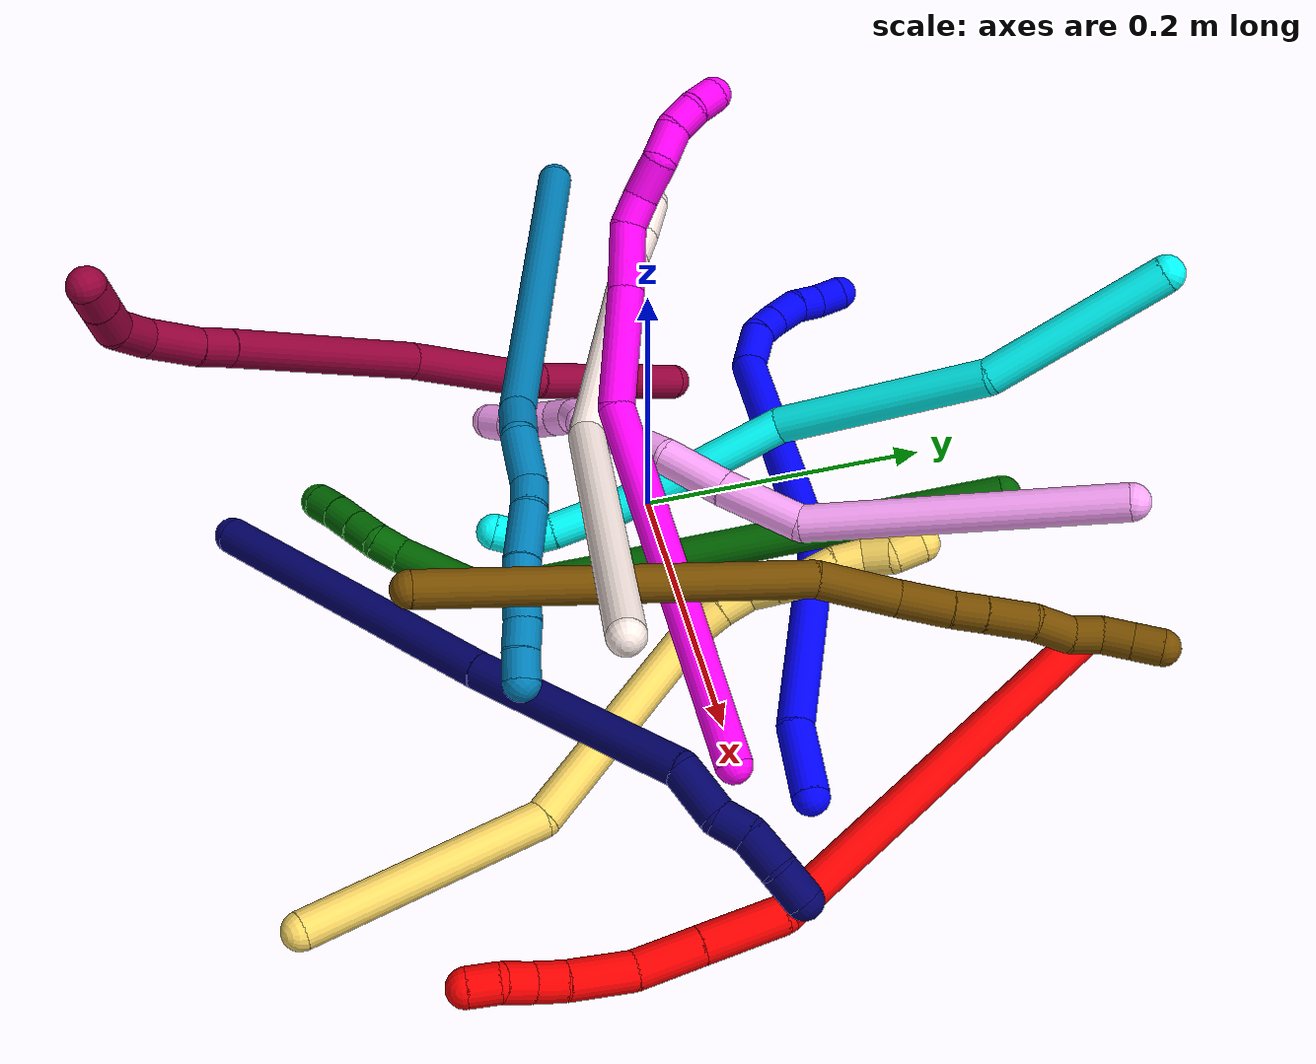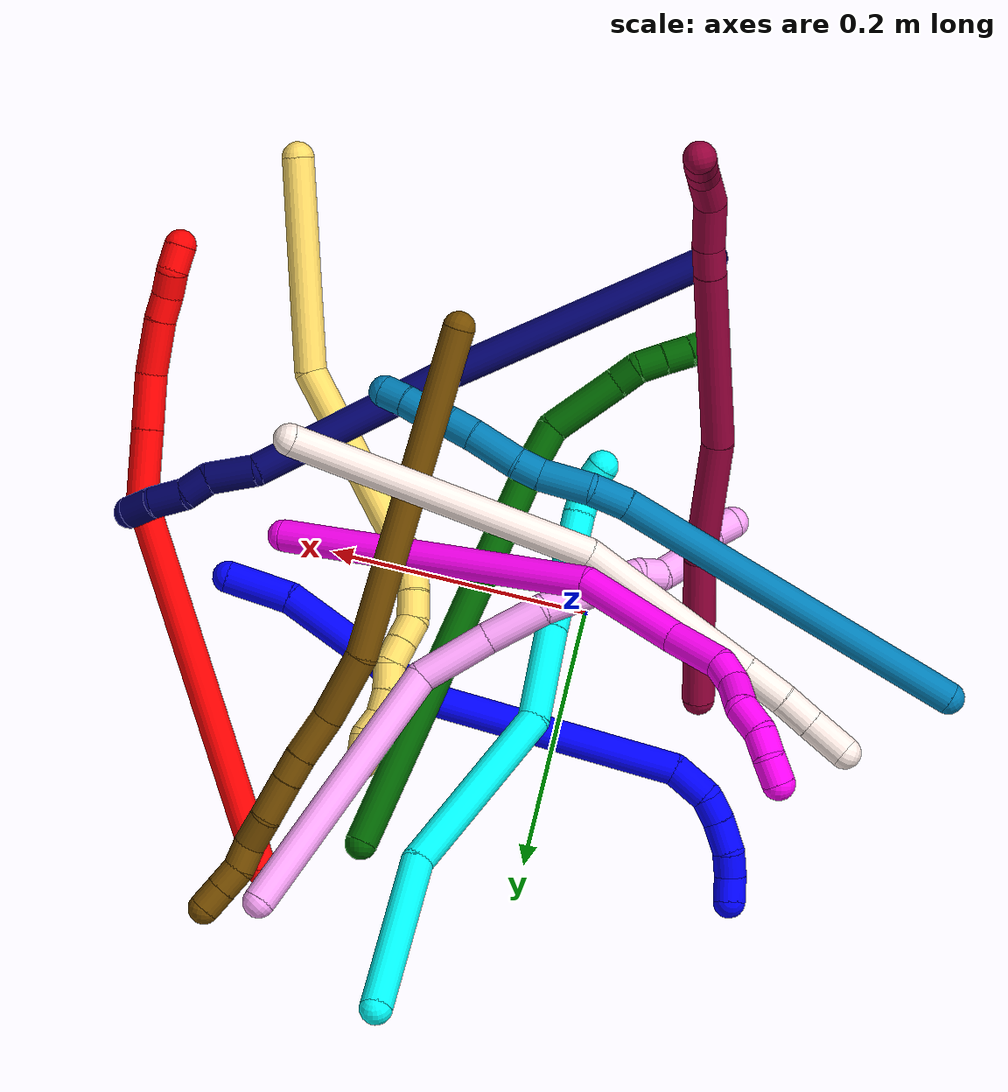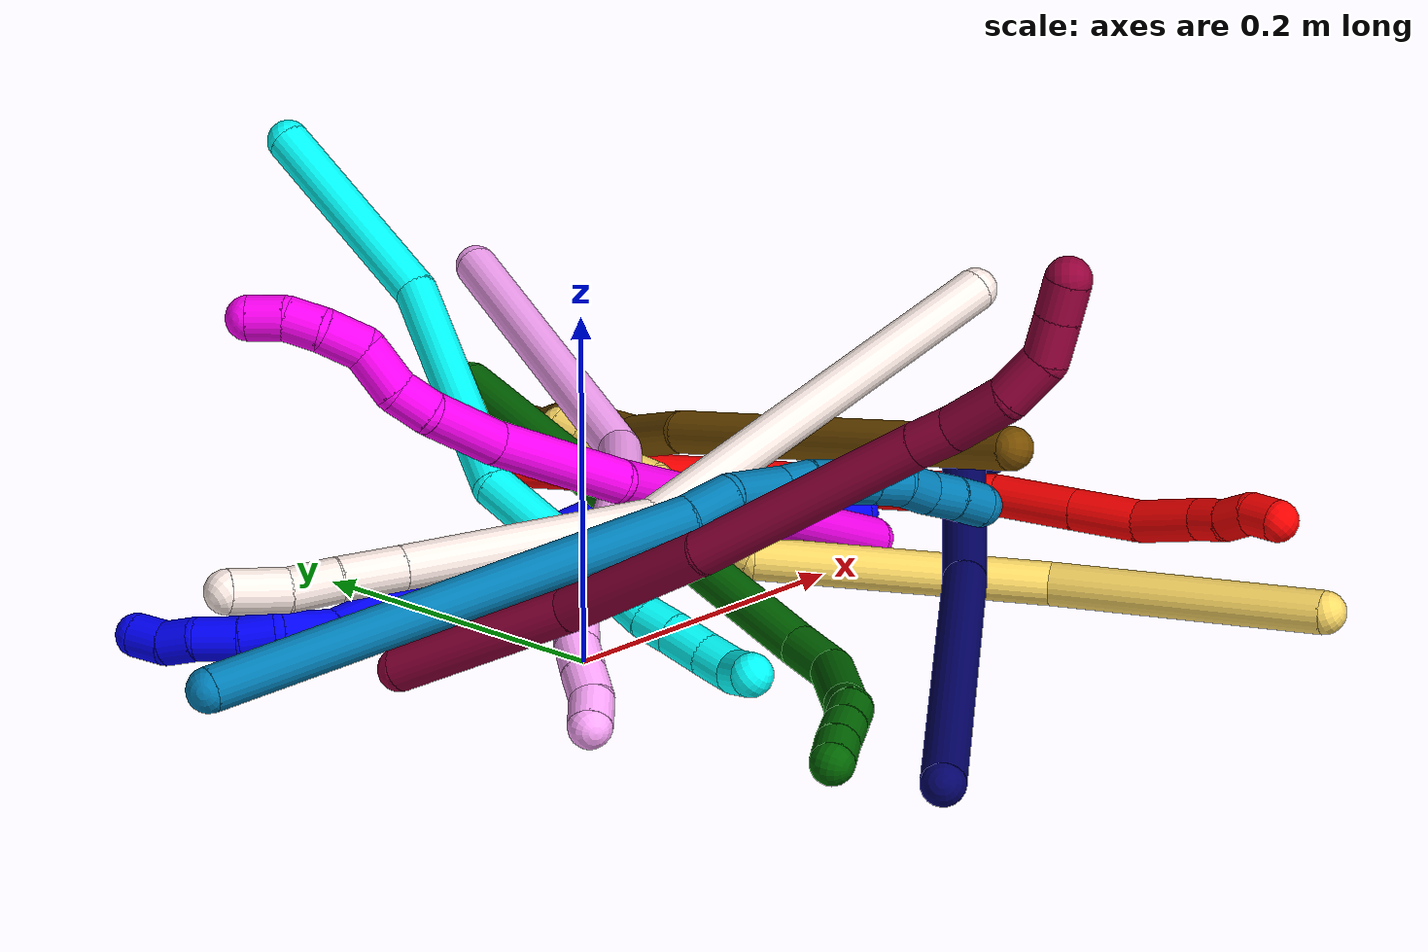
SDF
<sdf version="1.7">
 <world name="default">
  <plugin name="TubeGeneratorPlugin" filename="libtube_generator_plugin.so"/>
  <model name="photoneo_s_sensor">
   <static>1</static>
   <pose>0 0 2 1.57079 1.57079 3.14159</pose>
   <link name="link">
    <inertial><mass>0.1</mass></inertial>
    <sensor name="sensor" type="depth">
     <update_rate>30</update_rate>
     <camera>
      <horizontal_fov>1.22</horizontal_fov>
      <image><width>1920</width><height>1200</height><format>B8G8R8</format></image>
      <clip><near>0.1</near><far>4</far></clip>
      <depth_camera><output>points</output></depth_camera>
     </camera>
     <plugin name="camera_plugin" filename="libgazebo_ros_depth_camera.so">
      <baseline>0.2</baseline>
      <alwaysOn>1</alwaysOn>
      <updateRate>0.0</updateRate>
      <cameraName>camera_ir</cameraName>
      <imageTopicName>/camera/color/image_raw</imageTopicName>
      <cameraInfoTopicName>/camera/color/camera_info</cameraInfoTopicName>
      <depthImageTopicName>/camera/depth/image_raw</depthImageTopicName>
      <depthImageCameraInfoTopicName>/camera/depth/camera_info</depthImageCameraInfoTopicName>
      <pointCloudTopicName>/camera/depth/points</pointCloudTopicName>
      <frameName>fr_optical</frameName>
      <pointCloudCutoff>0.1</pointCloudCutoff>
      <pointCloudCutoffMax>2.0</pointCloudCutoffMax>
      <distortionK1>0</distortionK1>
      <distortionK2>0</distortionK2>
      <distortionK3>0</distortionK3>
      <distortionT1>0</distortionT1>
      <distortionT2>0</distortionT2>
      <CxPrime>0</CxPrime>
      <Cx>0</Cx>
      <Cy>0</Cy>
      <focalLength>0</focalLength>
      <hackBaseline>0</hackBaseline>
     </plugin>
    </sensor>
   </link>
  </model>
  <gravity>0 0 -9.8</gravity>
  <magnetic_field>6e-06 2.3e-05 -4.2e-05</magnetic_field>
  <atmosphere type="adiabatic"/>
  <physics name="default_physics" default="0" type="ode">
   <max_step_size>0.003</max_step_size>
   <real_time_factor>1</real_time_factor>
   <real_time_update_rate>1000</real_time_update_rate>
   <max_contacts>10000</max_contacts>
   <ode>
    <solver>
     <type>quick</type>
     <iters>100</iters>
     <sor>1.3</sor>
     <use_dynamic_moi_rescaling>0</use_dynamic_moi_rescaling>
    </solver>
    <constraints>
     <contact_max_correcting_vel>0</contact_max_correcting_vel>
     <contact_surface_layer>0.001</contact_surface_layer>
     <cfm>0</cfm>
     <erp>0.2</erp>
    </constraints>
   </ode>
  </physics>
  <scene><ambient>0.4 0.4 0.4 1</ambient><background>0.7 0.7 0.7 1</background><shadows>0</shadows></scene>
  <audio><device>default</device></audio>
  <spherical_coordinates>
   <surface_model>EARTH_WGS84</surface_model>
   <latitude_deg>0</latitude_deg>
   <longitude_deg>0</longitude_deg>
   <elevation>0</elevation>
   <heading_deg>0</heading_deg>
  </spherical_coordinates>
  <model name="bin">
   <static>1</static>
   <link name="bottom">
    <collision name="collision-bottom">
     <pose>0 0 -0.01 0 -0 0</pose>
     <geometry><box><size>0.8 0.6 0.02</size></box></geometry>
     <surface>
      <friction><ode><mu>100</mu><mu2>100</mu2></ode></friction>
      <contact><collide_bitmask>65535</collide_bitmask></contact>
     </surface>
    </collision>
   </link>
   <link name="west_wall">
    <collision name="collision-west_wall">
     <pose>-0.41 0 0.1 0 -0 0</pose>
     <geometry><box><size>0.02 0.6 0.2</size></box></geometry>
     <surface>
      <friction><ode><mu>100</mu><mu2>100</mu2></ode></friction>
      <contact><collide_bitmask>65535</collide_bitmask></contact>
     </surface>
    </collision>
   </link>
   <link name="east_wall">
    <collision name="collision-east_wall">
     <pose>0.41 0 0.1 0 -0 0</pose>
     <geometry><box><size>0.02 0.6 0.2</size></box></geometry>
     <surface>
      <friction><ode><mu>100</mu><mu2>100</mu2></ode></friction>
      <contact><collide_bitmask>65535</collide_bitmask></contact>
     </surface>
    </collision>
   </link>
   <link name="south_wall">
    <collision name="collision-south_wall">
     <pose>0 -0.31 0.1 0 -0 0</pose>
     <geometry><box><size>0.8 0.02 0.2</size></box></geometry>
     <surface>
      <friction><ode><mu>100</mu><mu2>100</mu2></ode></friction>
      <contact><collide_bitmask>65535</collide_bitmask></contact>
     </surface>
    </collision>
   </link>
   <link name="north_wall">
    <collision name="collision-north_wall">
     <pose>0 0.31 0.1 0 -0 0</pose>
     <geometry><box><size>0.8 0.02 0.2</size></box></geometry>
     <surface>
      <friction><ode><mu>100</mu><mu2>100</mu2></ode></friction>
      <contact><collide_bitmask>65535</collide_bitmask></contact>
     </surface>
    </collision>
   </link>
  </model>
  <model name="1">
   <static>0</static>
   <link name="1">
    <collision name="collision-cylinder-e_1_1_4">
     <pose>-0.024528 0.004065 0.005872 -0.605521 -1.28746 0.460457</pose>
     <geometry><cylinder><radius>0.0125</radius><length>0.051093</length></cylinder></geometry>
     <surface>
      <friction><ode><mu>1.16</mu><mu2>1.16</mu2><slip1>0</slip1><slip2>0</slip2></ode></friction>
      <contact><ode><kp>1e+06</kp><kd>1</kd><max_vel>0</max_vel><min_depth>0.001</min_depth></ode></contact>
     </surface>
    </collision>
    <visual name="visual-cylinder-e_1_1_4">
     <pose>-0.024528 0.004065 0.005872 -0.605521 -1.28746 0.460457</pose>
     <geometry><cylinder><radius>0.0125</radius><length>0.051093</length></cylinder></geometry>
     <material><ambient>0 0 1 1</ambient></material>
    </visual>
    <collision name="collision-cylinder-e_2_4_5">
     <pose>-0.107501 0.037127 0.022198 -1.22479 -1.08546 0.801551</pose>
     <geometry><cylinder><radius>0.0125</radius><length>0.13215</length></cylinder></geometry>
     <surface>
      <friction><ode><mu>1.16</mu><mu2>1.16</mu2><slip1>0</slip1><slip2>0</slip2></ode></friction>
      <contact><ode><kp>1e+06</kp><kd>1</kd><max_vel>0</max_vel><min_depth>0.001</min_depth></ode></contact>
     </surface>
    </collision>
    <visual name="visual-cylinder-e_2_4_5">
     <pose>-0.107501 0.037127 0.022198 -1.22479 -1.08546 0.801551</pose>
     <geometry><cylinder><radius>0.0125</radius><length>0.13215</length></cylinder></geometry>
     <material><ambient>0 0 1 1</ambient></material>
    </visual>
    <collision name="collision-cylinder-e_3_5_6">
     <pose>-0.264787 0.071757 0.03803 -0.80844 -1.49217 0.753068</pose>
     <geometry><cylinder><radius>0.0125</radius><length>0.198295</length></cylinder></geometry>
     <surface>
      <friction><ode><mu>1.16</mu><mu2>1.16</mu2><slip1>0</slip1><slip2>0</slip2></ode></friction>
      <contact><ode><kp>1e+06</kp><kd>1</kd><max_vel>0</max_vel><min_depth>0.001</min_depth></ode></contact>
     </surface>
    </collision>
    <visual name="visual-cylinder-e_3_5_6">
     <pose>-0.264787 0.071757 0.03803 -0.80844 -1.49217 0.753068</pose>
     <geometry><cylinder><radius>0.0125</radius><length>0.198295</length></cylinder></geometry>
     <material><ambient>0 0 1 1</ambient></material>
    </visual>
    <collision name="collision-cylinder-e_4_6_7">
     <pose>-0.377422 0.085374 0.044812 -1.39671 -1.03943 0.895587</pose>
     <geometry><cylinder><radius>0.0125</radius><length>0.032001</length></cylinder></geometry>
     <surface>
      <friction><ode><mu>1.16</mu><mu2>1.16</mu2><slip1>0</slip1><slip2>0</slip2></ode></friction>
      <contact><ode><kp>1e+06</kp><kd>1</kd><max_vel>0</max_vel><min_depth>0.001</min_depth></ode></contact>
     </surface>
    </collision>
    <visual name="visual-cylinder-e_4_6_7">
     <pose>-0.377422 0.085374 0.044812 -1.39671 -1.03943 0.895587</pose>
     <geometry><cylinder><radius>0.0125</radius><length>0.032001</length></cylinder></geometry>
     <material><ambient>0 0 1 1</ambient></material>
    </visual>
    <collision name="collision-cylinder-e_5_7_8">
     <pose>-0.398178 0.100509 0.043163 -1.9744 -0.730211 1.04948</pose>
     <geometry><cylinder><radius>0.0125</radius><length>0.020873</length></cylinder></geometry>
     <surface>
      <friction><ode><mu>1.16</mu><mu2>1.16</mu2><slip1>0</slip1><slip2>0</slip2></ode></friction>
      <contact><ode><kp>1e+06</kp><kd>1</kd><max_vel>0</max_vel><min_depth>0.001</min_depth></ode></contact>
     </surface>
    </collision>
    <visual name="visual-cylinder-e_5_7_8">
     <pose>-0.398178 0.100509 0.043163 -1.9744 -0.730211 1.04948</pose>
     <geometry><cylinder><radius>0.0125</radius><length>0.020873</length></cylinder></geometry>
     <material><ambient>0 0 1 1</ambient></material>
    </visual>
    <collision name="collision-cylinder-e_6_8_9">
     <pose>-0.411932 0.117895 0.036889 -1.87557 -0.564379 0.752612</pose>
     <geometry><cylinder><radius>0.0125</radius><length>0.025399</length></cylinder></geometry>
     <surface>
      <friction><ode><mu>1.16</mu><mu2>1.16</mu2><slip1>0</slip1><slip2>0</slip2></ode></friction>
      <contact><ode><kp>1e+06</kp><kd>1</kd><max_vel>0</max_vel><min_depth>0.001</min_depth></ode></contact>
     </surface>
    </collision>
    <visual name="visual-cylinder-e_6_8_9">
     <pose>-0.411932 0.117895 0.036889 -1.87557 -0.564379 0.752612</pose>
     <geometry><cylinder><radius>0.0125</radius><length>0.025399</length></cylinder></geometry>
     <material><ambient>0 0 1 1</ambient></material>
    </visual>
    <collision name="collision-cylinder-e_7_9_10">
     <pose>-0.422207 0.136167 0.02875 -2.12013 -0.353987 0.617991</pose>
     <geometry><cylinder><radius>0.0125</radius><length>0.020089</length></cylinder></geometry>
     <surface>
      <friction><ode><mu>1.16</mu><mu2>1.16</mu2><slip1>0</slip1><slip2>0</slip2></ode></friction>
      <contact><ode><kp>1e+06</kp><kd>1</kd><max_vel>0</max_vel><min_depth>0.001</min_depth></ode></contact>
     </surface>
    </collision>
    <visual name="visual-cylinder-e_7_9_10">
     <pose>-0.422207 0.136167 0.02875 -2.12013 -0.353987 0.617991</pose>
     <geometry><cylinder><radius>0.0125</radius><length>0.020089</length></cylinder></geometry>
     <material><ambient>0 0 1 1</ambient></material>
    </visual>
    <collision name="collision-cylinder-e_8_10_2">
     <pose>-0.427539 0.153822 0.021586 -1.80005 -0.185177 0.232974</pose>
     <geometry><cylinder><radius>0.0125</radius><length>0.0201</length></cylinder></geometry>
     <surface>
      <friction><ode><mu>1.16</mu><mu2>1.16</mu2><slip1>0</slip1><slip2>0</slip2></ode></friction>
      <contact><ode><kp>1e+06</kp><kd>1</kd><max_vel>0</max_vel><min_depth>0.001</min_depth></ode></contact>
     </surface>
    </collision>
    <visual name="visual-cylinder-e_8_10_2">
     <pose>-0.427539 0.153822 0.021586 -1.80005 -0.185177 0.232974</pose>
     <geometry><cylinder><radius>0.0125</radius><length>0.0201</length></cylinder></geometry>
     <material><ambient>0 0 1 1</ambient></material>
    </visual>
    <collision name="collision-sphere-2">
     <pose>-0.429389 0.163442 0.019341 0 -0 0</pose>
     <geometry><sphere><radius>0.0125</radius></sphere></geometry>
     <surface>
      <friction><ode><mu>1.16</mu><mu2>1.16</mu2><slip1>0</slip1><slip2>0</slip2></ode></friction>
      <contact><ode><kp>1e+06</kp><kd>1</kd><max_vel>0</max_vel><min_depth>0.001</min_depth></ode></contact>
     </surface>
    </collision>
    <visual name="visual-sphere-2">
     <pose>-0.429389 0.163442 0.019341 0 -0 0</pose>
     <geometry><sphere><radius>0.0125</radius></sphere></geometry>
     <material><ambient>0 0 1 1</ambient></material>
    </visual>
    <collision name="collision-sphere-10">
     <pose>-0.425688 0.144202 0.023831 0 -0 0</pose>
     <geometry><sphere><radius>0.0125</radius></sphere></geometry>
     <surface>
      <friction><ode><mu>1.16</mu><mu2>1.16</mu2><slip1>0</slip1><slip2>0</slip2></ode></friction>
      <contact><ode><kp>1e+06</kp><kd>1</kd><max_vel>0</max_vel><min_depth>0.001</min_depth></ode></contact>
     </surface>
    </collision>
    <visual name="visual-sphere-10">
     <pose>-0.425688 0.144202 0.023831 0 -0 0</pose>
     <geometry><sphere><radius>0.0125</radius></sphere></geometry>
     <material><ambient>0 0 1 1</ambient></material>
    </visual>
    <collision name="collision-sphere-9">
     <pose>-0.418725 0.128131 0.033669 0 -0 0</pose>
     <geometry><sphere><radius>0.0125</radius></sphere></geometry>
     <surface>
      <friction><ode><mu>1.16</mu><mu2>1.16</mu2><slip1>0</slip1><slip2>0</slip2></ode></friction>
      <contact><ode><kp>1e+06</kp><kd>1</kd><max_vel>0</max_vel><min_depth>0.001</min_depth></ode></contact>
     </surface>
    </collision>
    <visual name="visual-sphere-9">
     <pose>-0.418725 0.128131 0.033669 0 -0 0</pose>
     <geometry><sphere><radius>0.0125</radius></sphere></geometry>
     <material><ambient>0 0 1 1</ambient></material>
    </visual>
    <collision name="collision-sphere-4">
     <pose>-0.049056 0.00813 0.011744 0 -0 0</pose>
     <geometry><sphere><radius>0.0125</radius></sphere></geometry>
     <surface>
      <friction><ode><mu>1.16</mu><mu2>1.16</mu2><slip1>0</slip1><slip2>0</slip2></ode></friction>
      <contact><ode><kp>1e+06</kp><kd>1</kd><max_vel>0</max_vel><min_depth>0.001</min_depth></ode></contact>
     </surface>
    </collision>
    <visual name="visual-sphere-4">
     <pose>-0.049056 0.00813 0.011744 0 -0 0</pose>
     <geometry><sphere><radius>0.0125</radius></sphere></geometry>
     <material><ambient>0 0 1 1</ambient></material>
    </visual>
    <collision name="collision-sphere-1">
     <geometry><sphere><radius>0.0125</radius></sphere></geometry>
     <surface>
      <friction><ode><mu>1.16</mu><mu2>1.16</mu2><slip1>0</slip1><slip2>0</slip2></ode></friction>
      <contact><ode><kp>1e+06</kp><kd>1</kd><max_vel>0</max_vel><min_depth>0.001</min_depth></ode></contact>
     </surface>
    </collision>
    <visual name="visual-sphere-1">
     <geometry><sphere><radius>0.0125</radius></sphere></geometry>
     <material><ambient>0 0 1 1</ambient></material>
    </visual>
    <collision name="collision-sphere-8">
     <pose>-0.405139 0.10766 0.040109 0 -0 0</pose>
     <geometry><sphere><radius>0.0125</radius></sphere></geometry>
     <surface>
      <friction><ode><mu>1.16</mu><mu2>1.16</mu2><slip1>0</slip1><slip2>0</slip2></ode></friction>
      <contact><ode><kp>1e+06</kp><kd>1</kd><max_vel>0</max_vel><min_depth>0.001</min_depth></ode></contact>
     </surface>
    </collision>
    <visual name="visual-sphere-8">
     <pose>-0.405139 0.10766 0.040109 0 -0 0</pose>
     <geometry><sphere><radius>0.0125</radius></sphere></geometry>
     <material><ambient>0 0 1 1</ambient></material>
    </visual>
    <collision name="collision-sphere-5">
     <pose>-0.165945 0.066125 0.032652 0 -0 0</pose>
     <geometry><sphere><radius>0.0125</radius></sphere></geometry>
     <surface>
      <friction><ode><mu>1.16</mu><mu2>1.16</mu2><slip1>0</slip1><slip2>0</slip2></ode></friction>
      <contact><ode><kp>1e+06</kp><kd>1</kd><max_vel>0</max_vel><min_depth>0.001</min_depth></ode></contact>
     </surface>
    </collision>
    <visual name="visual-sphere-5">
     <pose>-0.165945 0.066125 0.032652 0 -0 0</pose>
     <geometry><sphere><radius>0.0125</radius></sphere></geometry>
     <material><ambient>0 0 1 1</ambient></material>
    </visual>
    <collision name="collision-sphere-6">
     <pose>-0.363628 0.077388 0.043408 0 -0 0</pose>
     <geometry><sphere><radius>0.0125</radius></sphere></geometry>
     <surface>
      <friction><ode><mu>1.16</mu><mu2>1.16</mu2><slip1>0</slip1><slip2>0</slip2></ode></friction>
      <contact><ode><kp>1e+06</kp><kd>1</kd><max_vel>0</max_vel><min_depth>0.001</min_depth></ode></contact>
     </surface>
    </collision>
    <visual name="visual-sphere-6">
     <pose>-0.363628 0.077388 0.043408 0 -0 0</pose>
     <geometry><sphere><radius>0.0125</radius></sphere></geometry>
     <material><ambient>0 0 1 1</ambient></material>
    </visual>
    <collision name="collision-sphere-7">
     <pose>-0.391216 0.093359 0.046216 0 -0 0</pose>
     <geometry><sphere><radius>0.0125</radius></sphere></geometry>
     <surface>
      <friction><ode><mu>1.16</mu><mu2>1.16</mu2><slip1>0</slip1><slip2>0</slip2></ode></friction>
      <contact><ode><kp>1e+06</kp><kd>1</kd><max_vel>0</max_vel><min_depth>0.001</min_depth></ode></contact>
     </surface>
    </collision>
    <visual name="visual-sphere-7">
     <pose>-0.391216 0.093359 0.046216 0 -0 0</pose>
     <geometry><sphere><radius>0.0125</radius></sphere></geometry>
     <material><ambient>0 0 1 1</ambient></material>
    </visual>
    <inertial>
     <pose>-0.231784 0.065989 0.030116 0 -0 0</pose>
     <mass>0.5</mass>
     <inertia>
      <ixx>0.000186</ixx>
      <ixy>0</ixy>
      <ixz>0</ixz>
      <iyy>0.000957</iyy>
      <iyz>0</iyz>
      <izz>0.000717</izz>
     </inertia>
    </inertial>
   </link>
   <pose>0.273592 0.037473 0.011493 0.313706 -0.156507 -0.006843</pose>
  </model>
  <model name="2">
   <static>0</static>
   <link name="2">
    <collision name="collision-cylinder-e_1_1_4">
     <pose>0.040929 -0.117416 0.081852 0.962009 0.278521 0.146044</pose>
     <geometry><cylinder><radius>0.0125</radius><length>0.297735</length></cylinder></geometry>
     <surface>
      <friction><ode><mu>1.16</mu><mu2>1.16</mu2><slip1>0</slip1><slip2>0</slip2></ode></friction>
      <contact><ode><kp>1e+06</kp><kd>1</kd><max_vel>0</max_vel><min_depth>0.001</min_depth></ode></contact>
     </surface>
    </collision>
    <visual name="visual-cylinder-e_1_1_4">
     <pose>0.040929 -0.117416 0.081852 0.962009 0.278521 0.146044</pose>
     <geometry><cylinder><radius>0.0125</radius><length>0.297735</length></cylinder></geometry>
     <material><ambient>1 0 0 1</ambient></material>
    </visual>
    <collision name="collision-cylinder-e_2_4_5">
     <pose>0.081121 -0.260573 0.173646 1.20223 -0.02668 -0.018297</pose>
     <geometry><cylinder><radius>0.0125</radius><length>0.055209</length></cylinder></geometry>
     <surface>
      <friction><ode><mu>1.16</mu><mu2>1.16</mu2><slip1>0</slip1><slip2>0</slip2></ode></friction>
      <contact><ode><kp>1e+06</kp><kd>1</kd><max_vel>0</max_vel><min_depth>0.001</min_depth></ode></contact>
     </surface>
    </collision>
    <visual name="visual-cylinder-e_2_4_5">
     <pose>0.081121 -0.260573 0.173646 1.20223 -0.02668 -0.018297</pose>
     <geometry><cylinder><radius>0.0125</radius><length>0.055209</length></cylinder></geometry>
     <material><ambient>1 0 0 1</ambient></material>
    </visual>
    <collision name="collision-cylinder-e_3_5_6">
     <pose>0.079897 -0.306583 0.191466 1.20008 -0.022413 -0.015335</pose>
     <geometry><cylinder><radius>0.0125</radius><length>0.043501</length></cylinder></geometry>
     <surface>
      <friction><ode><mu>1.16</mu><mu2>1.16</mu2><slip1>0</slip1><slip2>0</slip2></ode></friction>
      <contact><ode><kp>1e+06</kp><kd>1</kd><max_vel>0</max_vel><min_depth>0.001</min_depth></ode></contact>
     </surface>
    </collision>
    <visual name="visual-cylinder-e_3_5_6">
     <pose>0.079897 -0.306583 0.191466 1.20008 -0.022413 -0.015335</pose>
     <geometry><cylinder><radius>0.0125</radius><length>0.043501</length></cylinder></geometry>
     <material><ambient>1 0 0 1</ambient></material>
    </visual>
    <collision name="collision-cylinder-e_4_6_7">
     <pose>0.07418 -0.345358 0.208826 1.09733 -0.246356 -0.151068</pose>
     <geometry><cylinder><radius>0.0125</radius><length>0.042885</length></cylinder></geometry>
     <surface>
      <friction><ode><mu>1.16</mu><mu2>1.16</mu2><slip1>0</slip1><slip2>0</slip2></ode></friction>
      <contact><ode><kp>1e+06</kp><kd>1</kd><max_vel>0</max_vel><min_depth>0.001</min_depth></ode></contact>
     </surface>
    </collision>
    <visual name="visual-cylinder-e_4_6_7">
     <pose>0.07418 -0.345358 0.208826 1.09733 -0.246356 -0.151068</pose>
     <geometry><cylinder><radius>0.0125</radius><length>0.042885</length></cylinder></geometry>
     <material><ambient>1 0 0 1</ambient></material>
    </visual>
    <collision name="collision-cylinder-e_5_7_8">
     <pose>0.065674 -0.372817 0.221859 1.1931 -0.328 -0.22382</pose>
     <geometry><cylinder><radius>0.0125</radius><length>0.020345</length></cylinder></geometry>
     <surface>
      <friction><ode><mu>1.16</mu><mu2>1.16</mu2><slip1>0</slip1><slip2>0</slip2></ode></friction>
      <contact><ode><kp>1e+06</kp><kd>1</kd><max_vel>0</max_vel><min_depth>0.001</min_depth></ode></contact>
     </surface>
    </collision>
    <visual name="visual-cylinder-e_5_7_8">
     <pose>0.065674 -0.372817 0.221859 1.1931 -0.328 -0.22382</pose>
     <geometry><cylinder><radius>0.0125</radius><length>0.020345</length></cylinder></geometry>
     <material><ambient>1 0 0 1</ambient></material>
    </visual>
    <collision name="collision-cylinder-e_6_8_9">
     <pose>0.058551 -0.389397 0.23069 0.965441 -0.393009 -0.207906</pose>
     <geometry><cylinder><radius>0.0125</radius><length>0.020087</length></cylinder></geometry>
     <surface>
      <friction><ode><mu>1.16</mu><mu2>1.16</mu2><slip1>0</slip1><slip2>0</slip2></ode></friction>
      <contact><ode><kp>1e+06</kp><kd>1</kd><max_vel>0</max_vel><min_depth>0.001</min_depth></ode></contact>
     </surface>
    </collision>
    <visual name="visual-cylinder-e_6_8_9">
     <pose>0.058551 -0.389397 0.23069 0.965441 -0.393009 -0.207906</pose>
     <geometry><cylinder><radius>0.0125</radius><length>0.020087</length></cylinder></geometry>
     <material><ambient>1 0 0 1</ambient></material>
    </visual>
    <collision name="collision-cylinder-e_7_9_2">
     <pose>0.052595 -0.406689 0.238114 1.35238 -0.209983 -0.168707</pose>
     <geometry><cylinder><radius>0.0125</radius><length>0.020239</length></cylinder></geometry>
     <surface>
      <friction><ode><mu>1.16</mu><mu2>1.16</mu2><slip1>0</slip1><slip2>0</slip2></ode></friction>
      <contact><ode><kp>1e+06</kp><kd>1</kd><max_vel>0</max_vel><min_depth>0.001</min_depth></ode></contact>
     </surface>
    </collision>
    <visual name="visual-cylinder-e_7_9_2">
     <pose>0.052595 -0.406689 0.238114 1.35238 -0.209983 -0.168707</pose>
     <geometry><cylinder><radius>0.0125</radius><length>0.020239</length></cylinder></geometry>
     <material><ambient>1 0 0 1</ambient></material>
    </visual>
    <collision name="collision-sphere-2">
     <pose>0.050486 -0.416351 0.240258 0 -0 0</pose>
     <geometry><sphere><radius>0.0125</radius></sphere></geometry>
     <surface>
      <friction><ode><mu>1.16</mu><mu2>1.16</mu2><slip1>0</slip1><slip2>0</slip2></ode></friction>
      <contact><ode><kp>1e+06</kp><kd>1</kd><max_vel>0</max_vel><min_depth>0.001</min_depth></ode></contact>
     </surface>
    </collision>
    <visual name="visual-sphere-2">
     <pose>0.050486 -0.416351 0.240258 0 -0 0</pose>
     <geometry><sphere><radius>0.0125</radius></sphere></geometry>
     <material><ambient>1 0 0 1</ambient></material>
    </visual>
    <collision name="collision-sphere-9">
     <pose>0.054704 -0.397027 0.235969 0 -0 0</pose>
     <geometry><sphere><radius>0.0125</radius></sphere></geometry>
     <surface>
      <friction><ode><mu>1.16</mu><mu2>1.16</mu2><slip1>0</slip1><slip2>0</slip2></ode></friction>
      <contact><ode><kp>1e+06</kp><kd>1</kd><max_vel>0</max_vel><min_depth>0.001</min_depth></ode></contact>
     </surface>
    </collision>
    <visual name="visual-sphere-9">
     <pose>0.054704 -0.397027 0.235969 0 -0 0</pose>
     <geometry><sphere><radius>0.0125</radius></sphere></geometry>
     <material><ambient>1 0 0 1</ambient></material>
    </visual>
    <collision name="collision-sphere-4">
     <pose>0.081857 -0.234832 0.163705 0 -0 0</pose>
     <geometry><sphere><radius>0.0125</radius></sphere></geometry>
     <surface>
      <friction><ode><mu>1.16</mu><mu2>1.16</mu2><slip1>0</slip1><slip2>0</slip2></ode></friction>
      <contact><ode><kp>1e+06</kp><kd>1</kd><max_vel>0</max_vel><min_depth>0.001</min_depth></ode></contact>
     </surface>
    </collision>
    <visual name="visual-sphere-4">
     <pose>0.081857 -0.234832 0.163705 0 -0 0</pose>
     <geometry><sphere><radius>0.0125</radius></sphere></geometry>
     <material><ambient>1 0 0 1</ambient></material>
    </visual>
    <collision name="collision-sphere-1">
     <geometry><sphere><radius>0.0125</radius></sphere></geometry>
     <surface>
      <friction><ode><mu>1.16</mu><mu2>1.16</mu2><slip1>0</slip1><slip2>0</slip2></ode></friction>
      <contact><ode><kp>1e+06</kp><kd>1</kd><max_vel>0</max_vel><min_depth>0.001</min_depth></ode></contact>
     </surface>
    </collision>
    <visual name="visual-sphere-1">
     <geometry><sphere><radius>0.0125</radius></sphere></geometry>
     <material><ambient>1 0 0 1</ambient></material>
    </visual>
    <collision name="collision-sphere-8">
     <pose>0.062397 -0.381768 0.22541 0 -0 0</pose>
     <geometry><sphere><radius>0.0125</radius></sphere></geometry>
     <surface>
      <friction><ode><mu>1.16</mu><mu2>1.16</mu2><slip1>0</slip1><slip2>0</slip2></ode></friction>
      <contact><ode><kp>1e+06</kp><kd>1</kd><max_vel>0</max_vel><min_depth>0.001</min_depth></ode></contact>
     </surface>
    </collision>
    <visual name="visual-sphere-8">
     <pose>0.062397 -0.381768 0.22541 0 -0 0</pose>
     <geometry><sphere><radius>0.0125</radius></sphere></geometry>
     <material><ambient>1 0 0 1</ambient></material>
    </visual>
    <collision name="collision-sphere-5">
     <pose>0.080384 -0.286315 0.183588 0 -0 0</pose>
     <geometry><sphere><radius>0.0125</radius></sphere></geometry>
     <surface>
      <friction><ode><mu>1.16</mu><mu2>1.16</mu2><slip1>0</slip1><slip2>0</slip2></ode></friction>
      <contact><ode><kp>1e+06</kp><kd>1</kd><max_vel>0</max_vel><min_depth>0.001</min_depth></ode></contact>
     </surface>
    </collision>
    <visual name="visual-sphere-5">
     <pose>0.080384 -0.286315 0.183588 0 -0 0</pose>
     <geometry><sphere><radius>0.0125</radius></sphere></geometry>
     <material><ambient>1 0 0 1</ambient></material>
    </visual>
    <collision name="collision-sphere-6">
     <pose>0.07941 -0.326851 0.199344 0 -0 0</pose>
     <geometry><sphere><radius>0.0125</radius></sphere></geometry>
     <surface>
      <friction><ode><mu>1.16</mu><mu2>1.16</mu2><slip1>0</slip1><slip2>0</slip2></ode></friction>
      <contact><ode><kp>1e+06</kp><kd>1</kd><max_vel>0</max_vel><min_depth>0.001</min_depth></ode></contact>
     </surface>
    </collision>
    <visual name="visual-sphere-6">
     <pose>0.07941 -0.326851 0.199344 0 -0 0</pose>
     <geometry><sphere><radius>0.0125</radius></sphere></geometry>
     <material><ambient>1 0 0 1</ambient></material>
    </visual>
    <collision name="collision-sphere-7">
     <pose>0.068951 -0.363865 0.218308 0 -0 0</pose>
     <geometry><sphere><radius>0.0125</radius></sphere></geometry>
     <surface>
      <friction><ode><mu>1.16</mu><mu2>1.16</mu2><slip1>0</slip1><slip2>0</slip2></ode></friction>
      <contact><ode><kp>1e+06</kp><kd>1</kd><max_vel>0</max_vel><min_depth>0.001</min_depth></ode></contact>
     </surface>
    </collision>
    <visual name="visual-sphere-7">
     <pose>0.068951 -0.363865 0.218308 0 -0 0</pose>
     <geometry><sphere><radius>0.0125</radius></sphere></geometry>
     <material><ambient>1 0 0 1</ambient></material>
    </visual>
    <inertial>
     <pose>0.053796 -0.202259 0.130416 0 -0 0</pose>
     <mass>0.5</mass>
     <inertia>
      <ixx>0.002451</ixx>
      <ixy>0</ixy>
      <ixz>0</ixz>
      <iyy>0.001613</iyy>
      <iyz>0</iyz>
      <izz>0.001193</izz>
     </inertia>
    </inertial>
   </link>
   <pose>0.196123 0.250231 0.011479 0.36717 0.696565 0.183422</pose>
  </model>
  <model name="3">
   <static>0</static>
   <link name="3">
    <collision name="collision-cylinder-e_1_1_4">
     <pose>-0.011948 -0.061802 -0.013841 1.79113 -0.186457 -0.23246</pose>
     <geometry><cylinder><radius>0.0125</radius><length>0.128901</length></cylinder></geometry>
     <surface>
      <friction><ode><mu>1.16</mu><mu2>1.16</mu2><slip1>0</slip1><slip2>0</slip2></ode></friction>
      <contact><ode><kp>1e+06</kp><kd>1</kd><max_vel>0</max_vel><min_depth>0.001</min_depth></ode></contact>
     </surface>
    </collision>
    <visual name="visual-cylinder-e_1_1_4">
     <pose>-0.011948 -0.061802 -0.013841 1.79113 -0.186457 -0.23246</pose>
     <geometry><cylinder><radius>0.0125</radius><length>0.128901</length></cylinder></geometry>
     <material><ambient>0.003922 1 0.996078 1</ambient></material>
    </visual>
    <collision name="collision-cylinder-e_2_4_5">
     <pose>-0.011278 -0.199842 -0.035353 1.67106 0.1632 0.180353</pose>
     <geometry><cylinder><radius>0.0125</radius><length>0.155309</length></cylinder></geometry>
     <surface>
      <friction><ode><mu>1.16</mu><mu2>1.16</mu2><slip1>0</slip1><slip2>0</slip2></ode></friction>
      <contact><ode><kp>1e+06</kp><kd>1</kd><max_vel>0</max_vel><min_depth>0.001</min_depth></ode></contact>
     </surface>
    </collision>
    <visual name="visual-cylinder-e_2_4_5">
     <pose>-0.011278 -0.199842 -0.035353 1.67106 0.1632 0.180353</pose>
     <geometry><cylinder><radius>0.0125</radius><length>0.155309</length></cylinder></geometry>
     <material><ambient>0.003922 1 0.996078 1</ambient></material>
    </visual>
    <collision name="collision-cylinder-e_3_5_6">
     <pose>-0.005933 -0.310667 -0.057218 1.96025 -0.192101 -0.285424</pose>
     <geometry><cylinder><radius>0.0125</radius><length>0.076176</length></cylinder></geometry>
     <surface>
      <friction><ode><mu>1.16</mu><mu2>1.16</mu2><slip1>0</slip1><slip2>0</slip2></ode></friction>
      <contact><ode><kp>1e+06</kp><kd>1</kd><max_vel>0</max_vel><min_depth>0.001</min_depth></ode></contact>
     </surface>
    </collision>
    <visual name="visual-cylinder-e_3_5_6">
     <pose>-0.005933 -0.310667 -0.057218 1.96025 -0.192101 -0.285424</pose>
     <geometry><cylinder><radius>0.0125</radius><length>0.076176</length></cylinder></geometry>
     <material><ambient>0.003922 1 0.996078 1</ambient></material>
    </visual>
    <collision name="collision-cylinder-e_4_6_7">
     <pose>-0.017044 -0.368493 -0.080454 1.94185 -0.152765 -0.222867</pose>
     <geometry><cylinder><radius>0.0125</radius><length>0.050458</length></cylinder></geometry>
     <surface>
      <friction><ode><mu>1.16</mu><mu2>1.16</mu2><slip1>0</slip1><slip2>0</slip2></ode></friction>
      <contact><ode><kp>1e+06</kp><kd>1</kd><max_vel>0</max_vel><min_depth>0.001</min_depth></ode></contact>
     </surface>
    </collision>
    <visual name="visual-cylinder-e_4_6_7">
     <pose>-0.017044 -0.368493 -0.080454 1.94185 -0.152765 -0.222867</pose>
     <geometry><cylinder><radius>0.0125</radius><length>0.050458</length></cylinder></geometry>
     <material><ambient>0.003922 1 0.996078 1</ambient></material>
    </visual>
    <collision name="collision-cylinder-e_5_7_8">
     <pose>-0.021966 -0.400433 -0.094931 2.12912 -0.10515 -0.189262</pose>
     <geometry><cylinder><radius>0.0125</radius><length>0.020633</length></cylinder></geometry>
     <surface>
      <friction><ode><mu>1.16</mu><mu2>1.16</mu2><slip1>0</slip1><slip2>0</slip2></ode></friction>
      <contact><ode><kp>1e+06</kp><kd>1</kd><max_vel>0</max_vel><min_depth>0.001</min_depth></ode></contact>
     </surface>
    </collision>
    <visual name="visual-cylinder-e_5_7_8">
     <pose>-0.021966 -0.400433 -0.094931 2.12912 -0.10515 -0.189262</pose>
     <geometry><cylinder><radius>0.0125</radius><length>0.020633</length></cylinder></geometry>
     <material><ambient>0.003922 1 0.996078 1</ambient></material>
    </visual>
    <collision name="collision-cylinder-e_6_8_9">
     <pose>-0.024434 -0.420214 -0.106894 2.10322 -0.107284 -0.18736</pose>
     <geometry><cylinder><radius>0.0125</radius><length>0.025869</length></cylinder></geometry>
     <surface>
      <friction><ode><mu>1.16</mu><mu2>1.16</mu2><slip1>0</slip1><slip2>0</slip2></ode></friction>
      <contact><ode><kp>1e+06</kp><kd>1</kd><max_vel>0</max_vel><min_depth>0.001</min_depth></ode></contact>
     </surface>
    </collision>
    <visual name="visual-cylinder-e_6_8_9">
     <pose>-0.024434 -0.420214 -0.106894 2.10322 -0.107284 -0.18736</pose>
     <geometry><cylinder><radius>0.0125</radius><length>0.025869</length></cylinder></geometry>
     <material><ambient>0.003922 1 0.996078 1</ambient></material>
    </visual>
    <collision name="collision-cylinder-e_7_9_10">
     <pose>-0.025902 -0.440694 -0.119486 2.14375 -0.007408 -0.013595</pose>
     <geometry><cylinder><radius>0.0125</radius><length>0.022373</length></cylinder></geometry>
     <surface>
      <friction><ode><mu>1.16</mu><mu2>1.16</mu2><slip1>0</slip1><slip2>0</slip2></ode></friction>
      <contact><ode><kp>1e+06</kp><kd>1</kd><max_vel>0</max_vel><min_depth>0.001</min_depth></ode></contact>
     </surface>
    </collision>
    <visual name="visual-cylinder-e_7_9_10">
     <pose>-0.025902 -0.440694 -0.119486 2.14375 -0.007408 -0.013595</pose>
     <geometry><cylinder><radius>0.0125</radius><length>0.022373</length></cylinder></geometry>
     <material><ambient>0.003922 1 0.996078 1</ambient></material>
    </visual>
    <collision name="collision-cylinder-e_8_10_2">
     <pose>-0.021694 -0.456169 -0.132445 2.41932 0.436799 1.06251</pose>
     <geometry><cylinder><radius>0.0125</radius><length>0.020282</length></cylinder></geometry>
     <surface>
      <friction><ode><mu>1.16</mu><mu2>1.16</mu2><slip1>0</slip1><slip2>0</slip2></ode></friction>
      <contact><ode><kp>1e+06</kp><kd>1</kd><max_vel>0</max_vel><min_depth>0.001</min_depth></ode></contact>
     </surface>
    </collision>
    <visual name="visual-cylinder-e_8_10_2">
     <pose>-0.021694 -0.456169 -0.132445 2.41932 0.436799 1.06251</pose>
     <geometry><cylinder><radius>0.0125</radius><length>0.020282</length></cylinder></geometry>
     <material><ambient>0.003922 1 0.996078 1</ambient></material>
    </visual>
    <collision name="collision-sphere-2">
     <pose>-0.017404 -0.462243 -0.139339 0 -0 0</pose>
     <geometry><sphere><radius>0.0125</radius></sphere></geometry>
     <surface>
      <friction><ode><mu>1.16</mu><mu2>1.16</mu2><slip1>0</slip1><slip2>0</slip2></ode></friction>
      <contact><ode><kp>1e+06</kp><kd>1</kd><max_vel>0</max_vel><min_depth>0.001</min_depth></ode></contact>
     </surface>
    </collision>
    <visual name="visual-sphere-2">
     <pose>-0.017404 -0.462243 -0.139339 0 -0 0</pose>
     <geometry><sphere><radius>0.0125</radius></sphere></geometry>
     <material><ambient>0.003922 1 0.996078 1</ambient></material>
    </visual>
    <collision name="collision-sphere-10">
     <pose>-0.025985 -0.450094 -0.125551 0 -0 0</pose>
     <geometry><sphere><radius>0.0125</radius></sphere></geometry>
     <surface>
      <friction><ode><mu>1.16</mu><mu2>1.16</mu2><slip1>0</slip1><slip2>0</slip2></ode></friction>
      <contact><ode><kp>1e+06</kp><kd>1</kd><max_vel>0</max_vel><min_depth>0.001</min_depth></ode></contact>
     </surface>
    </collision>
    <visual name="visual-sphere-10">
     <pose>-0.025985 -0.450094 -0.125551 0 -0 0</pose>
     <geometry><sphere><radius>0.0125</radius></sphere></geometry>
     <material><ambient>0.003922 1 0.996078 1</ambient></material>
    </visual>
    <collision name="collision-sphere-9">
     <pose>-0.025819 -0.431294 -0.113422 0 -0 0</pose>
     <geometry><sphere><radius>0.0125</radius></sphere></geometry>
     <surface>
      <friction><ode><mu>1.16</mu><mu2>1.16</mu2><slip1>0</slip1><slip2>0</slip2></ode></friction>
      <contact><ode><kp>1e+06</kp><kd>1</kd><max_vel>0</max_vel><min_depth>0.001</min_depth></ode></contact>
     </surface>
    </collision>
    <visual name="visual-sphere-9">
     <pose>-0.025819 -0.431294 -0.113422 0 -0 0</pose>
     <geometry><sphere><radius>0.0125</radius></sphere></geometry>
     <material><ambient>0.003922 1 0.996078 1</ambient></material>
    </visual>
    <collision name="collision-sphere-4">
     <pose>-0.023895 -0.123604 -0.027683 0 -0 0</pose>
     <geometry><sphere><radius>0.0125</radius></sphere></geometry>
     <surface>
      <friction><ode><mu>1.16</mu><mu2>1.16</mu2><slip1>0</slip1><slip2>0</slip2></ode></friction>
      <contact><ode><kp>1e+06</kp><kd>1</kd><max_vel>0</max_vel><min_depth>0.001</min_depth></ode></contact>
     </surface>
    </collision>
    <visual name="visual-sphere-4">
     <pose>-0.023895 -0.123604 -0.027683 0 -0 0</pose>
     <geometry><sphere><radius>0.0125</radius></sphere></geometry>
     <material><ambient>0.003922 1 0.996078 1</ambient></material>
    </visual>
    <collision name="collision-sphere-1">
     <geometry><sphere><radius>0.0125</radius></sphere></geometry>
     <surface>
      <friction><ode><mu>1.16</mu><mu2>1.16</mu2><slip1>0</slip1><slip2>0</slip2></ode></friction>
      <contact><ode><kp>1e+06</kp><kd>1</kd><max_vel>0</max_vel><min_depth>0.001</min_depth></ode></contact>
     </surface>
    </collision>
    <visual name="visual-sphere-1">
     <geometry><sphere><radius>0.0125</radius></sphere></geometry>
     <material><ambient>0.003922 1 0.996078 1</ambient></material>
    </visual>
    <collision name="collision-sphere-8">
     <pose>-0.023049 -0.409134 -0.100366 0 -0 0</pose>
     <geometry><sphere><radius>0.0125</radius></sphere></geometry>
     <surface>
      <friction><ode><mu>1.16</mu><mu2>1.16</mu2><slip1>0</slip1><slip2>0</slip2></ode></friction>
      <contact><ode><kp>1e+06</kp><kd>1</kd><max_vel>0</max_vel><min_depth>0.001</min_depth></ode></contact>
     </surface>
    </collision>
    <visual name="visual-sphere-8">
     <pose>-0.023049 -0.409134 -0.100366 0 -0 0</pose>
     <geometry><sphere><radius>0.0125</radius></sphere></geometry>
     <material><ambient>0.003922 1 0.996078 1</ambient></material>
    </visual>
    <collision name="collision-sphere-5">
     <pose>0.001339 -0.27608 -0.043022 0 -0 0</pose>
     <geometry><sphere><radius>0.0125</radius></sphere></geometry>
     <surface>
      <friction><ode><mu>1.16</mu><mu2>1.16</mu2><slip1>0</slip1><slip2>0</slip2></ode></friction>
      <contact><ode><kp>1e+06</kp><kd>1</kd><max_vel>0</max_vel><min_depth>0.001</min_depth></ode></contact>
     </surface>
    </collision>
    <visual name="visual-sphere-5">
     <pose>0.001339 -0.27608 -0.043022 0 -0 0</pose>
     <geometry><sphere><radius>0.0125</radius></sphere></geometry>
     <material><ambient>0.003922 1 0.996078 1</ambient></material>
    </visual>
    <collision name="collision-sphere-6">
     <pose>-0.013205 -0.345255 -0.071413 0 -0 0</pose>
     <geometry><sphere><radius>0.0125</radius></sphere></geometry>
     <surface>
      <friction><ode><mu>1.16</mu><mu2>1.16</mu2><slip1>0</slip1><slip2>0</slip2></ode></friction>
      <contact><ode><kp>1e+06</kp><kd>1</kd><max_vel>0</max_vel><min_depth>0.001</min_depth></ode></contact>
     </surface>
    </collision>
    <visual name="visual-sphere-6">
     <pose>-0.013205 -0.345255 -0.071413 0 -0 0</pose>
     <geometry><sphere><radius>0.0125</radius></sphere></geometry>
     <material><ambient>0.003922 1 0.996078 1</ambient></material>
    </visual>
    <collision name="collision-sphere-7">
     <pose>-0.020883 -0.391731 -0.089496 0 -0 0</pose>
     <geometry><sphere><radius>0.0125</radius></sphere></geometry>
     <surface>
      <friction><ode><mu>1.16</mu><mu2>1.16</mu2><slip1>0</slip1><slip2>0</slip2></ode></friction>
      <contact><ode><kp>1e+06</kp><kd>1</kd><max_vel>0</max_vel><min_depth>0.001</min_depth></ode></contact>
     </surface>
    </collision>
    <visual name="visual-sphere-7">
     <pose>-0.020883 -0.391731 -0.089496 0 -0 0</pose>
     <geometry><sphere><radius>0.0125</radius></sphere></geometry>
     <material><ambient>0.003922 1 0.996078 1</ambient></material>
    </visual>
    <inertial>
     <pose>-0.013417 -0.239013 -0.051553 0 -0 0</pose>
     <mass>0.5</mass>
     <inertia>
      <ixx>0.000541</ixx>
      <ixy>0</ixy>
      <ixz>0</ixz>
      <iyy>-0.000108</iyy>
      <iyz>0</iyz>
      <izz>0.000523</izz>
     </inertia>
    </inertial>
   </link>
   <pose>0.083641 0.317374 0.224796 2.37868 -0.404752 -3.14091</pose>
  </model>
  <model name="4">
   <static>0</static>
   <link name="4">
    <collision name="collision-cylinder-e_1_1_4">
     <pose>-0.028613 0.010473 -0.102244 -3.03952 -0.271518 2.4259</pose>
     <geometry><cylinder><radius>0.0125</radius><length>0.213375</length></cylinder></geometry>
     <surface>
      <friction><ode><mu>1.16</mu><mu2>1.16</mu2><slip1>0</slip1><slip2>0</slip2></ode></friction>
      <contact><ode><kp>1e+06</kp><kd>1</kd><max_vel>0</max_vel><min_depth>0.001</min_depth></ode></contact>
     </surface>
    </collision>
    <visual name="visual-cylinder-e_1_1_4">
     <pose>-0.028613 0.010473 -0.102244 -3.03952 -0.271518 2.4259</pose>
     <geometry><cylinder><radius>0.0125</radius><length>0.213375</length></cylinder></geometry>
     <material><ambient>1 0.65098 0.996078 1</ambient></material>
    </visual>
    <collision name="collision-cylinder-e_2_4_5">
     <pose>-0.056627 0.012631 -0.23256 2.85364 0.020458 0.140881</pose>
     <geometry><cylinder><radius>0.0125</radius><length>0.058568</length></cylinder></geometry>
     <surface>
      <friction><ode><mu>1.16</mu><mu2>1.16</mu2><slip1>0</slip1><slip2>0</slip2></ode></friction>
      <contact><ode><kp>1e+06</kp><kd>1</kd><max_vel>0</max_vel><min_depth>0.001</min_depth></ode></contact>
     </surface>
    </collision>
    <visual name="visual-cylinder-e_2_4_5">
     <pose>-0.056627 0.012631 -0.23256 2.85364 0.020458 0.140881</pose>
     <geometry><cylinder><radius>0.0125</radius><length>0.058568</length></cylinder></geometry>
     <material><ambient>1 0.65098 0.996078 1</ambient></material>
    </visual>
    <collision name="collision-cylinder-e_3_5_6">
     <pose>-0.054337 -0.003419 -0.282972 2.80825 0.0714 0.418382</pose>
     <geometry><cylinder><radius>0.0125</radius><length>0.047402</length></cylinder></geometry>
     <surface>
      <friction><ode><mu>1.16</mu><mu2>1.16</mu2><slip1>0</slip1><slip2>0</slip2></ode></friction>
      <contact><ode><kp>1e+06</kp><kd>1</kd><max_vel>0</max_vel><min_depth>0.001</min_depth></ode></contact>
     </surface>
    </collision>
    <visual name="visual-cylinder-e_3_5_6">
     <pose>-0.054337 -0.003419 -0.282972 2.80825 0.0714 0.418382</pose>
     <geometry><cylinder><radius>0.0125</radius><length>0.047402</length></cylinder></geometry>
     <material><ambient>1 0.65098 0.996078 1</ambient></material>
    </visual>
    <collision name="collision-cylinder-e_4_6_7">
     <pose>-0.061808 -0.029589 -0.339894 2.65185 -0.229653 -0.864824</pose>
     <geometry><cylinder><radius>0.0125</radius><length>0.080492</length></cylinder></geometry>
     <surface>
      <friction><ode><mu>1.16</mu><mu2>1.16</mu2><slip1>0</slip1><slip2>0</slip2></ode></friction>
      <contact><ode><kp>1e+06</kp><kd>1</kd><max_vel>0</max_vel><min_depth>0.001</min_depth></ode></contact>
     </surface>
    </collision>
    <visual name="visual-cylinder-e_4_6_7">
     <pose>-0.061808 -0.029589 -0.339894 2.65185 -0.229653 -0.864824</pose>
     <geometry><cylinder><radius>0.0125</radius><length>0.080492</length></cylinder></geometry>
     <material><ambient>1 0.65098 0.996078 1</ambient></material>
    </visual>
    <collision name="collision-cylinder-e_5_7_8">
     <pose>-0.0755 -0.055123 -0.379924 2.22528 -0.468709 -0.90171</pose>
     <geometry><cylinder><radius>0.0125</radius><length>0.02006</length></cylinder></geometry>
     <surface>
      <friction><ode><mu>1.16</mu><mu2>1.16</mu2><slip1>0</slip1><slip2>0</slip2></ode></friction>
      <contact><ode><kp>1e+06</kp><kd>1</kd><max_vel>0</max_vel><min_depth>0.001</min_depth></ode></contact>
     </surface>
    </collision>
    <visual name="visual-cylinder-e_5_7_8">
     <pose>-0.0755 -0.055123 -0.379924 2.22528 -0.468709 -0.90171</pose>
     <geometry><cylinder><radius>0.0125</radius><length>0.02006</length></cylinder></geometry>
     <material><ambient>1 0.65098 0.996078 1</ambient></material>
    </visual>
    <collision name="collision-cylinder-e_6_8_9">
     <pose>-0.085599 -0.065079 -0.393194 2.79149 -0.589323 -2.08632</pose>
     <geometry><cylinder><radius>0.0125</radius><length>0.020035</length></cylinder></geometry>
     <surface>
      <friction><ode><mu>1.16</mu><mu2>1.16</mu2><slip1>0</slip1><slip2>0</slip2></ode></friction>
      <contact><ode><kp>1e+06</kp><kd>1</kd><max_vel>0</max_vel><min_depth>0.001</min_depth></ode></contact>
     </surface>
    </collision>
    <visual name="visual-cylinder-e_6_8_9">
     <pose>-0.085599 -0.065079 -0.393194 2.79149 -0.589323 -2.08632</pose>
     <geometry><cylinder><radius>0.0125</radius><length>0.020035</length></cylinder></geometry>
     <material><ambient>1 0.65098 0.996078 1</ambient></material>
    </visual>
    <collision name="collision-cylinder-e_7_9_10">
     <pose>-0.095752 -0.069155 -0.409825 3.004 -0.476122 -2.58825</pose>
     <geometry><cylinder><radius>0.0125</radius><length>0.02001</length></cylinder></geometry>
     <surface>
      <friction><ode><mu>1.16</mu><mu2>1.16</mu2><slip1>0</slip1><slip2>0</slip2></ode></friction>
      <contact><ode><kp>1e+06</kp><kd>1</kd><max_vel>0</max_vel><min_depth>0.001</min_depth></ode></contact>
     </surface>
    </collision>
    <visual name="visual-cylinder-e_7_9_10">
     <pose>-0.095752 -0.069155 -0.409825 3.004 -0.476122 -2.58825</pose>
     <geometry><cylinder><radius>0.0125</radius><length>0.02001</length></cylinder></geometry>
     <material><ambient>1 0.65098 0.996078 1</ambient></material>
    </visual>
    <collision name="collision-cylinder-e_8_10_11">
     <pose>-0.104966 -0.071157 -0.427484 3.0534 -0.480196 -2.78495</pose>
     <geometry><cylinder><radius>0.0125</radius><length>0.020038</length></cylinder></geometry>
     <surface>
      <friction><ode><mu>1.16</mu><mu2>1.16</mu2><slip1>0</slip1><slip2>0</slip2></ode></friction>
      <contact><ode><kp>1e+06</kp><kd>1</kd><max_vel>0</max_vel><min_depth>0.001</min_depth></ode></contact>
     </surface>
    </collision>
    <visual name="visual-cylinder-e_8_10_11">
     <pose>-0.104966 -0.071157 -0.427484 3.0534 -0.480196 -2.78495</pose>
     <geometry><cylinder><radius>0.0125</radius><length>0.020038</length></cylinder></geometry>
     <material><ambient>1 0.65098 0.996078 1</ambient></material>
    </visual>
    <collision name="collision-cylinder-e_9_11_2">
     <pose>-0.113522 -0.075464 -0.444842 2.74877 -0.403209 -1.5976</pose>
     <geometry><cylinder><radius>0.0125</radius><length>0.02002</length></cylinder></geometry>
     <surface>
      <friction><ode><mu>1.16</mu><mu2>1.16</mu2><slip1>0</slip1><slip2>0</slip2></ode></friction>
      <contact><ode><kp>1e+06</kp><kd>1</kd><max_vel>0</max_vel><min_depth>0.001</min_depth></ode></contact>
     </surface>
    </collision>
    <visual name="visual-cylinder-e_9_11_2">
     <pose>-0.113522 -0.075464 -0.444842 2.74877 -0.403209 -1.5976</pose>
     <geometry><cylinder><radius>0.0125</radius><length>0.02002</length></cylinder></geometry>
     <material><ambient>1 0.65098 0.996078 1</ambient></material>
    </visual>
    <collision name="collision-sphere-2">
     <pose>-0.11745 -0.078989 -0.453348 0 -0 0</pose>
     <geometry><sphere><radius>0.0125</radius></sphere></geometry>
     <surface>
      <friction><ode><mu>1.16</mu><mu2>1.16</mu2><slip1>0</slip1><slip2>0</slip2></ode></friction>
      <contact><ode><kp>1e+06</kp><kd>1</kd><max_vel>0</max_vel><min_depth>0.001</min_depth></ode></contact>
     </surface>
    </collision>
    <visual name="visual-sphere-2">
     <pose>-0.11745 -0.078989 -0.453348 0 -0 0</pose>
     <geometry><sphere><radius>0.0125</radius></sphere></geometry>
     <material><ambient>1 0.65098 0.996078 1</ambient></material>
    </visual>
    <collision name="collision-sphere-11">
     <pose>-0.109594 -0.07194 -0.436335 0 -0 0</pose>
     <geometry><sphere><radius>0.0125</radius></sphere></geometry>
     <surface>
      <friction><ode><mu>1.16</mu><mu2>1.16</mu2><slip1>0</slip1><slip2>0</slip2></ode></friction>
      <contact><ode><kp>1e+06</kp><kd>1</kd><max_vel>0</max_vel><min_depth>0.001</min_depth></ode></contact>
     </surface>
    </collision>
    <visual name="visual-sphere-11">
     <pose>-0.109594 -0.07194 -0.436335 0 -0 0</pose>
     <geometry><sphere><radius>0.0125</radius></sphere></geometry>
     <material><ambient>1 0.65098 0.996078 1</ambient></material>
    </visual>
    <collision name="collision-sphere-10">
     <pose>-0.100338 -0.070374 -0.418633 0 -0 0</pose>
     <geometry><sphere><radius>0.0125</radius></sphere></geometry>
     <surface>
      <friction><ode><mu>1.16</mu><mu2>1.16</mu2><slip1>0</slip1><slip2>0</slip2></ode></friction>
      <contact><ode><kp>1e+06</kp><kd>1</kd><max_vel>0</max_vel><min_depth>0.001</min_depth></ode></contact>
     </surface>
    </collision>
    <visual name="visual-sphere-10">
     <pose>-0.100338 -0.070374 -0.418633 0 -0 0</pose>
     <geometry><sphere><radius>0.0125</radius></sphere></geometry>
     <material><ambient>1 0.65098 0.996078 1</ambient></material>
    </visual>
    <collision name="collision-sphere-9">
     <pose>-0.091166 -0.067935 -0.401016 0 -0 0</pose>
     <geometry><sphere><radius>0.0125</radius></sphere></geometry>
     <surface>
      <friction><ode><mu>1.16</mu><mu2>1.16</mu2><slip1>0</slip1><slip2>0</slip2></ode></friction>
      <contact><ode><kp>1e+06</kp><kd>1</kd><max_vel>0</max_vel><min_depth>0.001</min_depth></ode></contact>
     </surface>
    </collision>
    <visual name="visual-sphere-9">
     <pose>-0.091166 -0.067935 -0.401016 0 -0 0</pose>
     <geometry><sphere><radius>0.0125</radius></sphere></geometry>
     <material><ambient>1 0.65098 0.996078 1</ambient></material>
    </visual>
    <collision name="collision-sphere-4">
     <pose>-0.057226 0.020946 -0.204488 0 -0 0</pose>
     <geometry><sphere><radius>0.0125</radius></sphere></geometry>
     <surface>
      <friction><ode><mu>1.16</mu><mu2>1.16</mu2><slip1>0</slip1><slip2>0</slip2></ode></friction>
      <contact><ode><kp>1e+06</kp><kd>1</kd><max_vel>0</max_vel><min_depth>0.001</min_depth></ode></contact>
     </surface>
    </collision>
    <visual name="visual-sphere-4">
     <pose>-0.057226 0.020946 -0.204488 0 -0 0</pose>
     <geometry><sphere><radius>0.0125</radius></sphere></geometry>
     <material><ambient>1 0.65098 0.996078 1</ambient></material>
    </visual>
    <collision name="collision-sphere-1">
     <geometry><sphere><radius>0.0125</radius></sphere></geometry>
     <surface>
      <friction><ode><mu>1.16</mu><mu2>1.16</mu2><slip1>0</slip1><slip2>0</slip2></ode></friction>
      <contact><ode><kp>1e+06</kp><kd>1</kd><max_vel>0</max_vel><min_depth>0.001</min_depth></ode></contact>
     </surface>
    </collision>
    <visual name="visual-sphere-1">
     <geometry><sphere><radius>0.0125</radius></sphere></geometry>
     <material><ambient>1 0.65098 0.996078 1</ambient></material>
    </visual>
    <collision name="collision-sphere-8">
     <pose>-0.080031 -0.062222 -0.385371 0 -0 0</pose>
     <geometry><sphere><radius>0.0125</radius></sphere></geometry>
     <surface>
      <friction><ode><mu>1.16</mu><mu2>1.16</mu2><slip1>0</slip1><slip2>0</slip2></ode></friction>
      <contact><ode><kp>1e+06</kp><kd>1</kd><max_vel>0</max_vel><min_depth>0.001</min_depth></ode></contact>
     </surface>
    </collision>
    <visual name="visual-sphere-8">
     <pose>-0.080031 -0.062222 -0.385371 0 -0 0</pose>
     <geometry><sphere><radius>0.0125</radius></sphere></geometry>
     <material><ambient>1 0.65098 0.996078 1</ambient></material>
    </visual>
    <collision name="collision-sphere-5">
     <pose>-0.056028 0.004316 -0.260633 0 -0 0</pose>
     <geometry><sphere><radius>0.0125</radius></sphere></geometry>
     <surface>
      <friction><ode><mu>1.16</mu><mu2>1.16</mu2><slip1>0</slip1><slip2>0</slip2></ode></friction>
      <contact><ode><kp>1e+06</kp><kd>1</kd><max_vel>0</max_vel><min_depth>0.001</min_depth></ode></contact>
     </surface>
    </collision>
    <visual name="visual-sphere-5">
     <pose>-0.056028 0.004316 -0.260633 0 -0 0</pose>
     <geometry><sphere><radius>0.0125</radius></sphere></geometry>
     <material><ambient>1 0.65098 0.996078 1</ambient></material>
    </visual>
    <collision name="collision-sphere-6">
     <pose>-0.052646 -0.011155 -0.305311 0 -0 0</pose>
     <geometry><sphere><radius>0.0125</radius></sphere></geometry>
     <surface>
      <friction><ode><mu>1.16</mu><mu2>1.16</mu2><slip1>0</slip1><slip2>0</slip2></ode></friction>
      <contact><ode><kp>1e+06</kp><kd>1</kd><max_vel>0</max_vel><min_depth>0.001</min_depth></ode></contact>
     </surface>
    </collision>
    <visual name="visual-sphere-6">
     <pose>-0.052646 -0.011155 -0.305311 0 -0 0</pose>
     <geometry><sphere><radius>0.0125</radius></sphere></geometry>
     <material><ambient>1 0.65098 0.996078 1</ambient></material>
    </visual>
    <collision name="collision-sphere-7">
     <pose>-0.070969 -0.048024 -0.374477 0 -0 0</pose>
     <geometry><sphere><radius>0.0125</radius></sphere></geometry>
     <surface>
      <friction><ode><mu>1.16</mu><mu2>1.16</mu2><slip1>0</slip1><slip2>0</slip2></ode></friction>
      <contact><ode><kp>1e+06</kp><kd>1</kd><max_vel>0</max_vel><min_depth>0.001</min_depth></ode></contact>
     </surface>
    </collision>
    <visual name="visual-sphere-7">
     <pose>-0.070969 -0.048024 -0.374477 0 -0 0</pose>
     <geometry><sphere><radius>0.0125</radius></sphere></geometry>
     <material><ambient>1 0.65098 0.996078 1</ambient></material>
    </visual>
    <inertial>
     <pose>-0.052988 -0.012599 -0.234761 0 -0 0</pose>
     <mass>0.5</mass>
     <inertia>
      <ixx>-6.3e-05</ixx>
      <ixy>0</ixy>
      <ixz>0</ixz>
      <iyy>0.001061</iyy>
      <iyz>0</iyz>
      <izz>0.000149</izz>
     </inertia>
    </inertial>
   </link>
   <pose>0.188194 0.267157 0.135465 1.59685 -1.47865 2.60193</pose>
  </model>
  <model name="5">
   <static>0</static>
   <link name="5">
    <collision name="collision-cylinder-e_1_1_4">
     <pose>-0.013303 0.025041 -0.077639 -2.8296 -0.161655 0.95122</pose>
     <geometry><cylinder><radius>0.0125</radius><length>0.16531</length></cylinder></geometry>
     <surface>
      <friction><ode><mu>1.16</mu><mu2>1.16</mu2><slip1>0</slip1><slip2>0</slip2></ode></friction>
      <contact><ode><kp>1e+06</kp><kd>1</kd><max_vel>0</max_vel><min_depth>0.001</min_depth></ode></contact>
     </surface>
    </collision>
    <visual name="visual-cylinder-e_1_1_4">
     <pose>-0.013303 0.025041 -0.077639 -2.8296 -0.161655 0.95122</pose>
     <geometry><cylinder><radius>0.0125</radius><length>0.16531</length></cylinder></geometry>
     <material><ambient>1 0.858824 0.4 1</ambient></material>
    </visual>
    <collision name="collision-cylinder-e_2_4_5">
     <pose>-0.070848 0.05573 -0.22751 -3.06356 -0.548193 2.86569</pose>
     <geometry><cylinder><radius>0.0125</radius><length>0.169784</length></cylinder></geometry>
     <surface>
      <friction><ode><mu>1.16</mu><mu2>1.16</mu2><slip1>0</slip1><slip2>0</slip2></ode></friction>
      <contact><ode><kp>1e+06</kp><kd>1</kd><max_vel>0</max_vel><min_depth>0.001</min_depth></ode></contact>
     </surface>
    </collision>
    <visual name="visual-cylinder-e_2_4_5">
     <pose>-0.070848 0.05573 -0.22751 -3.06356 -0.548193 2.86569</pose>
     <geometry><cylinder><radius>0.0125</radius><length>0.169784</length></cylinder></geometry>
     <material><ambient>1 0.858824 0.4 1</ambient></material>
    </visual>
    <collision name="collision-cylinder-e_3_5_6">
     <pose>-0.119962 0.067182 -0.307572 -2.50363 -0.463655 1.2412</pose>
     <geometry><cylinder><radius>0.0125</radius><length>0.021795</length></cylinder></geometry>
     <surface>
      <friction><ode><mu>1.16</mu><mu2>1.16</mu2><slip1>0</slip1><slip2>0</slip2></ode></friction>
      <contact><ode><kp>1e+06</kp><kd>1</kd><max_vel>0</max_vel><min_depth>0.001</min_depth></ode></contact>
     </surface>
    </collision>
    <visual name="visual-cylinder-e_3_5_6">
     <pose>-0.119962 0.067182 -0.307572 -2.50363 -0.463655 1.2412</pose>
     <geometry><cylinder><radius>0.0125</radius><length>0.021795</length></cylinder></geometry>
     <material><ambient>1 0.858824 0.4 1</ambient></material>
    </visual>
    <collision name="collision-cylinder-e_4_6_7">
     <pose>-0.128486 0.079052 -0.323874 -2.5203 -0.336918 0.974331</pose>
     <geometry><cylinder><radius>0.0125</radius><length>0.02208</length></cylinder></geometry>
     <surface>
      <friction><ode><mu>1.16</mu><mu2>1.16</mu2><slip1>0</slip1><slip2>0</slip2></ode></friction>
      <contact><ode><kp>1e+06</kp><kd>1</kd><max_vel>0</max_vel><min_depth>0.001</min_depth></ode></contact>
     </surface>
    </collision>
    <visual name="visual-cylinder-e_4_6_7">
     <pose>-0.128486 0.079052 -0.323874 -2.5203 -0.336918 0.974331</pose>
     <geometry><cylinder><radius>0.0125</radius><length>0.02208</length></cylinder></geometry>
     <material><ambient>1 0.858824 0.4 1</ambient></material>
    </visual>
    <collision name="collision-cylinder-e_5_7_8">
     <pose>-0.132696 0.093592 -0.338011 -2.16 -0.054917 0.102696</pose>
     <geometry><cylinder><radius>0.0125</radius><length>0.020418</length></cylinder></geometry>
     <surface>
      <friction><ode><mu>1.16</mu><mu2>1.16</mu2><slip1>0</slip1><slip2>0</slip2></ode></friction>
      <contact><ode><kp>1e+06</kp><kd>1</kd><max_vel>0</max_vel><min_depth>0.001</min_depth></ode></contact>
     </surface>
    </collision>
    <visual name="visual-cylinder-e_5_7_8">
     <pose>-0.132696 0.093592 -0.338011 -2.16 -0.054917 0.102696</pose>
     <geometry><cylinder><radius>0.0125</radius><length>0.020418</length></cylinder></geometry>
     <material><ambient>1 0.858824 0.4 1</ambient></material>
    </visual>
    <collision name="collision-cylinder-e_6_8_9">
     <pose>-0.133831 0.110313 -0.349383 -2.17625 -0.057262 0.109198</pose>
     <geometry><cylinder><radius>0.0125</radius><length>0.020089</length></cylinder></geometry>
     <surface>
      <friction><ode><mu>1.16</mu><mu2>1.16</mu2><slip1>0</slip1><slip2>0</slip2></ode></friction>
      <contact><ode><kp>1e+06</kp><kd>1</kd><max_vel>0</max_vel><min_depth>0.001</min_depth></ode></contact>
     </surface>
    </collision>
    <visual name="visual-cylinder-e_6_8_9">
     <pose>-0.133831 0.110313 -0.349383 -2.17625 -0.057262 0.109198</pose>
     <geometry><cylinder><radius>0.0125</radius><length>0.020089</length></cylinder></geometry>
     <material><ambient>1 0.858824 0.4 1</ambient></material>
    </visual>
    <collision name="collision-cylinder-e_7_9_10">
     <pose>-0.137053 0.123781 -0.363444 -2.58285 -0.2625 0.862545</pose>
     <geometry><cylinder><radius>0.0125</radius><length>0.020401</length></cylinder></geometry>
     <surface>
      <friction><ode><mu>1.16</mu><mu2>1.16</mu2><slip1>0</slip1><slip2>0</slip2></ode></friction>
      <contact><ode><kp>1e+06</kp><kd>1</kd><max_vel>0</max_vel><min_depth>0.001</min_depth></ode></contact>
     </surface>
    </collision>
    <visual name="visual-cylinder-e_7_9_10">
     <pose>-0.137053 0.123781 -0.363444 -2.58285 -0.2625 0.862545</pose>
     <geometry><cylinder><radius>0.0125</radius><length>0.020401</length></cylinder></geometry>
     <material><ambient>1 0.858824 0.4 1</ambient></material>
    </visual>
    <collision name="collision-cylinder-e_8_10_11">
     <pose>-0.140044 0.135146 -0.379722 -2.48224 -0.034261 0.100056</pose>
     <geometry><cylinder><radius>0.0125</radius><length>0.020067</length></cylinder></geometry>
     <surface>
      <friction><ode><mu>1.16</mu><mu2>1.16</mu2><slip1>0</slip1><slip2>0</slip2></ode></friction>
      <contact><ode><kp>1e+06</kp><kd>1</kd><max_vel>0</max_vel><min_depth>0.001</min_depth></ode></contact>
     </surface>
    </collision>
    <visual name="visual-cylinder-e_8_10_11">
     <pose>-0.140044 0.135146 -0.379722 -2.48224 -0.034261 0.100056</pose>
     <geometry><cylinder><radius>0.0125</radius><length>0.020067</length></cylinder></geometry>
     <material><ambient>1 0.858824 0.4 1</ambient></material>
    </visual>
    <collision name="collision-cylinder-e_9_11_12">
     <pose>-0.139606 0.150005 -0.392519 -2.08038 0.078068 -0.132928</pose>
     <geometry><cylinder><radius>0.0125</radius><length>0.02003</length></cylinder></geometry>
     <surface>
      <friction><ode><mu>1.16</mu><mu2>1.16</mu2><slip1>0</slip1><slip2>0</slip2></ode></friction>
      <contact><ode><kp>1e+06</kp><kd>1</kd><max_vel>0</max_vel><min_depth>0.001</min_depth></ode></contact>
     </surface>
    </collision>
    <visual name="visual-cylinder-e_9_11_12">
     <pose>-0.139606 0.150005 -0.392519 -2.08038 0.078068 -0.132928</pose>
     <geometry><cylinder><radius>0.0125</radius><length>0.02003</length></cylinder></geometry>
     <material><ambient>1 0.858824 0.4 1</ambient></material>
    </visual>
    <collision name="collision-cylinder-e_10_12_2">
     <pose>-0.140533 0.164527 -0.405366 -2.51237 -0.171415 0.516263</pose>
     <geometry><cylinder><radius>0.0125</radius><length>0.020025</length></cylinder></geometry>
     <surface>
      <friction><ode><mu>1.16</mu><mu2>1.16</mu2><slip1>0</slip1><slip2>0</slip2></ode></friction>
      <contact><ode><kp>1e+06</kp><kd>1</kd><max_vel>0</max_vel><min_depth>0.001</min_depth></ode></contact>
     </surface>
    </collision>
    <visual name="visual-cylinder-e_10_12_2">
     <pose>-0.140533 0.164527 -0.405366 -2.51237 -0.171415 0.516263</pose>
     <geometry><cylinder><radius>0.0125</radius><length>0.020025</length></cylinder></geometry>
     <material><ambient>1 0.858824 0.4 1</ambient></material>
    </visual>
    <collision name="collision-sphere-2">
     <pose>-0.142241 0.170333 -0.413342 0 -0 0</pose>
     <geometry><sphere><radius>0.0125</radius></sphere></geometry>
     <surface>
      <friction><ode><mu>1.16</mu><mu2>1.16</mu2><slip1>0</slip1><slip2>0</slip2></ode></friction>
      <contact><ode><kp>1e+06</kp><kd>1</kd><max_vel>0</max_vel><min_depth>0.001</min_depth></ode></contact>
     </surface>
    </collision>
    <visual name="visual-sphere-2">
     <pose>-0.142241 0.170333 -0.413342 0 -0 0</pose>
     <geometry><sphere><radius>0.0125</radius></sphere></geometry>
     <material><ambient>1 0.858824 0.4 1</ambient></material>
    </visual>
    <collision name="collision-sphere-12">
     <pose>-0.138825 0.158721 -0.397389 0 -0 0</pose>
     <geometry><sphere><radius>0.0125</radius></sphere></geometry>
     <surface>
      <friction><ode><mu>1.16</mu><mu2>1.16</mu2><slip1>0</slip1><slip2>0</slip2></ode></friction>
      <contact><ode><kp>1e+06</kp><kd>1</kd><max_vel>0</max_vel><min_depth>0.001</min_depth></ode></contact>
     </surface>
    </collision>
    <visual name="visual-sphere-12">
     <pose>-0.138825 0.158721 -0.397389 0 -0 0</pose>
     <geometry><sphere><radius>0.0125</radius></sphere></geometry>
     <material><ambient>1 0.858824 0.4 1</ambient></material>
    </visual>
    <collision name="collision-sphere-11">
     <pose>-0.140387 0.141289 -0.387648 0 -0 0</pose>
     <geometry><sphere><radius>0.0125</radius></sphere></geometry>
     <surface>
      <friction><ode><mu>1.16</mu><mu2>1.16</mu2><slip1>0</slip1><slip2>0</slip2></ode></friction>
      <contact><ode><kp>1e+06</kp><kd>1</kd><max_vel>0</max_vel><min_depth>0.001</min_depth></ode></contact>
     </surface>
    </collision>
    <visual name="visual-sphere-11">
     <pose>-0.140387 0.141289 -0.387648 0 -0 0</pose>
     <geometry><sphere><radius>0.0125</radius></sphere></geometry>
     <material><ambient>1 0.858824 0.4 1</ambient></material>
    </visual>
    <collision name="collision-sphere-10">
     <pose>-0.1397 0.129003 -0.371797 0 -0 0</pose>
     <geometry><sphere><radius>0.0125</radius></sphere></geometry>
     <surface>
      <friction><ode><mu>1.16</mu><mu2>1.16</mu2><slip1>0</slip1><slip2>0</slip2></ode></friction>
      <contact><ode><kp>1e+06</kp><kd>1</kd><max_vel>0</max_vel><min_depth>0.001</min_depth></ode></contact>
     </surface>
    </collision>
    <visual name="visual-sphere-10">
     <pose>-0.1397 0.129003 -0.371797 0 -0 0</pose>
     <geometry><sphere><radius>0.0125</radius></sphere></geometry>
     <material><ambient>1 0.858824 0.4 1</ambient></material>
    </visual>
    <collision name="collision-sphere-9">
     <pose>-0.134406 0.118558 -0.355091 0 -0 0</pose>
     <geometry><sphere><radius>0.0125</radius></sphere></geometry>
     <surface>
      <friction><ode><mu>1.16</mu><mu2>1.16</mu2><slip1>0</slip1><slip2>0</slip2></ode></friction>
      <contact><ode><kp>1e+06</kp><kd>1</kd><max_vel>0</max_vel><min_depth>0.001</min_depth></ode></contact>
     </surface>
    </collision>
    <visual name="visual-sphere-9">
     <pose>-0.134406 0.118558 -0.355091 0 -0 0</pose>
     <geometry><sphere><radius>0.0125</radius></sphere></geometry>
     <material><ambient>1 0.858824 0.4 1</ambient></material>
    </visual>
    <collision name="collision-sphere-4">
     <pose>-0.026607 0.050082 -0.155278 0 -0 0</pose>
     <geometry><sphere><radius>0.0125</radius></sphere></geometry>
     <surface>
      <friction><ode><mu>1.16</mu><mu2>1.16</mu2><slip1>0</slip1><slip2>0</slip2></ode></friction>
      <contact><ode><kp>1e+06</kp><kd>1</kd><max_vel>0</max_vel><min_depth>0.001</min_depth></ode></contact>
     </surface>
    </collision>
    <visual name="visual-sphere-4">
     <pose>-0.026607 0.050082 -0.155278 0 -0 0</pose>
     <geometry><sphere><radius>0.0125</radius></sphere></geometry>
     <material><ambient>1 0.858824 0.4 1</ambient></material>
    </visual>
    <collision name="collision-sphere-1">
     <geometry><sphere><radius>0.0125</radius></sphere></geometry>
     <surface>
      <friction><ode><mu>1.16</mu><mu2>1.16</mu2><slip1>0</slip1><slip2>0</slip2></ode></friction>
      <contact><ode><kp>1e+06</kp><kd>1</kd><max_vel>0</max_vel><min_depth>0.001</min_depth></ode></contact>
     </surface>
    </collision>
    <visual name="visual-sphere-1">
     <geometry><sphere><radius>0.0125</radius></sphere></geometry>
     <material><ambient>1 0.858824 0.4 1</ambient></material>
    </visual>
    <collision name="collision-sphere-8">
     <pose>-0.133256 0.102067 -0.343676 0 -0 0</pose>
     <geometry><sphere><radius>0.0125</radius></sphere></geometry>
     <surface>
      <friction><ode><mu>1.16</mu><mu2>1.16</mu2><slip1>0</slip1><slip2>0</slip2></ode></friction>
      <contact><ode><kp>1e+06</kp><kd>1</kd><max_vel>0</max_vel><min_depth>0.001</min_depth></ode></contact>
     </surface>
    </collision>
    <visual name="visual-sphere-8">
     <pose>-0.133256 0.102067 -0.343676 0 -0 0</pose>
     <geometry><sphere><radius>0.0125</radius></sphere></geometry>
     <material><ambient>1 0.858824 0.4 1</ambient></material>
    </visual>
    <collision name="collision-sphere-5">
     <pose>-0.115089 0.061378 -0.299742 0 -0 0</pose>
     <geometry><sphere><radius>0.0125</radius></sphere></geometry>
     <surface>
      <friction><ode><mu>1.16</mu><mu2>1.16</mu2><slip1>0</slip1><slip2>0</slip2></ode></friction>
      <contact><ode><kp>1e+06</kp><kd>1</kd><max_vel>0</max_vel><min_depth>0.001</min_depth></ode></contact>
     </surface>
    </collision>
    <visual name="visual-sphere-5">
     <pose>-0.115089 0.061378 -0.299742 0 -0 0</pose>
     <geometry><sphere><radius>0.0125</radius></sphere></geometry>
     <material><ambient>1 0.858824 0.4 1</ambient></material>
    </visual>
    <collision name="collision-sphere-6">
     <pose>-0.124836 0.072987 -0.315402 0 -0 0</pose>
     <geometry><sphere><radius>0.0125</radius></sphere></geometry>
     <surface>
      <friction><ode><mu>1.16</mu><mu2>1.16</mu2><slip1>0</slip1><slip2>0</slip2></ode></friction>
      <contact><ode><kp>1e+06</kp><kd>1</kd><max_vel>0</max_vel><min_depth>0.001</min_depth></ode></contact>
     </surface>
    </collision>
    <visual name="visual-sphere-6">
     <pose>-0.124836 0.072987 -0.315402 0 -0 0</pose>
     <geometry><sphere><radius>0.0125</radius></sphere></geometry>
     <material><ambient>1 0.858824 0.4 1</ambient></material>
    </visual>
    <collision name="collision-sphere-7">
     <pose>-0.132135 0.085117 -0.332347 0 -0 0</pose>
     <geometry><sphere><radius>0.0125</radius></sphere></geometry>
     <surface>
      <friction><ode><mu>1.16</mu><mu2>1.16</mu2><slip1>0</slip1><slip2>0</slip2></ode></friction>
      <contact><ode><kp>1e+06</kp><kd>1</kd><max_vel>0</max_vel><min_depth>0.001</min_depth></ode></contact>
     </surface>
    </collision>
    <visual name="visual-sphere-7">
     <pose>-0.132135 0.085117 -0.332347 0 -0 0</pose>
     <geometry><sphere><radius>0.0125</radius></sphere></geometry>
     <material><ambient>1 0.858824 0.4 1</ambient></material>
    </visual>
    <inertial>
     <pose>-0.072589 0.06495 -0.220503 0 -0 0</pose>
     <mass>0.5</mass>
     <inertia>
      <ixx>0.000286</ixx>
      <ixy>0</ixy>
      <ixz>0</ixz>
      <iyy>0.000623</iyy>
      <iyz>0</iyz>
      <izz>9.6e-05</izz>
     </inertia>
    </inertial>
   </link>
   <pose>0.297175 -0.288507 0.020417 1.0368 0.754794 0.025374</pose>
  </model>
  <model name="6">
   <static>0</static>
   <link name="6">
    <collision name="collision-cylinder-e_1_1_4">
     <pose>-0.044264 -0.039773 0.150544 0.258294 -0.276969 -0.036198</pose>
     <geometry><cylinder><radius>0.0125</radius><length>0.323757</length></cylinder></geometry>
     <surface>
      <friction><ode><mu>1.16</mu><mu2>1.16</mu2><slip1>0</slip1><slip2>0</slip2></ode></friction>
      <contact><ode><kp>1e+06</kp><kd>1</kd><max_vel>0</max_vel><min_depth>0.001</min_depth></ode></contact>
     </surface>
    </collision>
    <visual name="visual-cylinder-e_1_1_4">
     <pose>-0.044264 -0.039773 0.150544 0.258294 -0.276969 -0.036198</pose>
     <geometry><cylinder><radius>0.0125</radius><length>0.323757</length></cylinder></geometry>
     <material><ambient>0 0.392157 0.003922 1</ambient></material>
    </visual>
    <collision name="collision-cylinder-e_2_4_5">
     <pose>-0.09496 -0.082604 0.316007 0.202164 -0.399558 -0.041068</pose>
     <geometry><cylinder><radius>0.0125</radius><length>0.033064</length></cylinder></geometry>
     <surface>
      <friction><ode><mu>1.16</mu><mu2>1.16</mu2><slip1>0</slip1><slip2>0</slip2></ode></friction>
      <contact><ode><kp>1e+06</kp><kd>1</kd><max_vel>0</max_vel><min_depth>0.001</min_depth></ode></contact>
     </surface>
    </collision>
    <visual name="visual-cylinder-e_2_4_5">
     <pose>-0.09496 -0.082604 0.316007 0.202164 -0.399558 -0.041068</pose>
     <geometry><cylinder><radius>0.0125</radius><length>0.033064</length></cylinder></geometry>
     <material><ambient>0 0.392157 0.003922 1</ambient></material>
    </visual>
    <collision name="collision-cylinder-e_3_5_6">
     <pose>-0.124784 -0.092071 0.349481 0.332606 -0.87264 -0.156219</pose>
     <geometry><cylinder><radius>0.0125</radius><length>0.061076</length></cylinder></geometry>
     <surface>
      <friction><ode><mu>1.16</mu><mu2>1.16</mu2><slip1>0</slip1><slip2>0</slip2></ode></friction>
      <contact><ode><kp>1e+06</kp><kd>1</kd><max_vel>0</max_vel><min_depth>0.001</min_depth></ode></contact>
     </surface>
    </collision>
    <visual name="visual-cylinder-e_3_5_6">
     <pose>-0.124784 -0.092071 0.349481 0.332606 -0.87264 -0.156219</pose>
     <geometry><cylinder><radius>0.0125</radius><length>0.061076</length></cylinder></geometry>
     <material><ambient>0 0.392157 0.003922 1</ambient></material>
    </visual>
    <collision name="collision-cylinder-e_4_6_7">
     <pose>-0.156425 -0.098642 0.37382 0.027886 -0.958989 -0.014501</pose>
     <geometry><cylinder><radius>0.0125</radius><length>0.020153</length></cylinder></geometry>
     <surface>
      <friction><ode><mu>1.16</mu><mu2>1.16</mu2><slip1>0</slip1><slip2>0</slip2></ode></friction>
      <contact><ode><kp>1e+06</kp><kd>1</kd><max_vel>0</max_vel><min_depth>0.001</min_depth></ode></contact>
     </surface>
    </collision>
    <visual name="visual-cylinder-e_4_6_7">
     <pose>-0.156425 -0.098642 0.37382 0.027886 -0.958989 -0.014501</pose>
     <geometry><cylinder><radius>0.0125</radius><length>0.020153</length></cylinder></geometry>
     <material><ambient>0 0.392157 0.003922 1</ambient></material>
    </visual>
    <collision name="collision-cylinder-e_5_7_8">
     <pose>-0.173448 -0.102945 0.38356 0.808496 -0.992569 -0.455277</pose>
     <geometry><cylinder><radius>0.0125</radius><length>0.020954</length></cylinder></geometry>
     <surface>
      <friction><ode><mu>1.16</mu><mu2>1.16</mu2><slip1>0</slip1><slip2>0</slip2></ode></friction>
      <contact><ode><kp>1e+06</kp><kd>1</kd><max_vel>0</max_vel><min_depth>0.001</min_depth></ode></contact>
     </surface>
    </collision>
    <visual name="visual-cylinder-e_5_7_8">
     <pose>-0.173448 -0.102945 0.38356 0.808496 -0.992569 -0.455277</pose>
     <geometry><cylinder><radius>0.0125</radius><length>0.020954</length></cylinder></geometry>
     <material><ambient>0 0.392157 0.003922 1</ambient></material>
    </visual>
    <collision name="collision-cylinder-e_6_8_9">
     <pose>-0.190874 -0.111714 0.391231 0.894049 -0.969551 -0.494647</pose>
     <geometry><cylinder><radius>0.0125</radius><length>0.020985</length></cylinder></geometry>
     <surface>
      <friction><ode><mu>1.16</mu><mu2>1.16</mu2><slip1>0</slip1><slip2>0</slip2></ode></friction>
      <contact><ode><kp>1e+06</kp><kd>1</kd><max_vel>0</max_vel><min_depth>0.001</min_depth></ode></contact>
     </surface>
    </collision>
    <visual name="visual-cylinder-e_6_8_9">
     <pose>-0.190874 -0.111714 0.391231 0.894049 -0.969551 -0.494647</pose>
     <geometry><cylinder><radius>0.0125</radius><length>0.020985</length></cylinder></geometry>
     <material><ambient>0 0.392157 0.003922 1</ambient></material>
    </visual>
    <collision name="collision-cylinder-e_7_9_2">
     <pose>-0.207376 -0.121025 0.399018 0.855428 -0.901843 -0.434478</pose>
     <geometry><cylinder><radius>0.0125</radius><length>0.020011</length></cylinder></geometry>
     <surface>
      <friction><ode><mu>1.16</mu><mu2>1.16</mu2><slip1>0</slip1><slip2>0</slip2></ode></friction>
      <contact><ode><kp>1e+06</kp><kd>1</kd><max_vel>0</max_vel><min_depth>0.001</min_depth></ode></contact>
     </surface>
    </collision>
    <visual name="visual-cylinder-e_7_9_2">
     <pose>-0.207376 -0.121025 0.399018 0.855428 -0.901843 -0.434478</pose>
     <geometry><cylinder><radius>0.0125</radius><length>0.020011</length></cylinder></geometry>
     <material><ambient>0 0.392157 0.003922 1</ambient></material>
    </visual>
    <collision name="collision-sphere-2">
     <pose>-0.215225 -0.125709 0.403088 0 -0 0</pose>
     <geometry><sphere><radius>0.0125</radius></sphere></geometry>
     <surface>
      <friction><ode><mu>1.16</mu><mu2>1.16</mu2><slip1>0</slip1><slip2>0</slip2></ode></friction>
      <contact><ode><kp>1e+06</kp><kd>1</kd><max_vel>0</max_vel><min_depth>0.001</min_depth></ode></contact>
     </surface>
    </collision>
    <visual name="visual-sphere-2">
     <pose>-0.215225 -0.125709 0.403088 0 -0 0</pose>
     <geometry><sphere><radius>0.0125</radius></sphere></geometry>
     <material><ambient>0 0.392157 0.003922 1</ambient></material>
    </visual>
    <collision name="collision-sphere-9">
     <pose>-0.199527 -0.116341 0.394948 0 -0 0</pose>
     <geometry><sphere><radius>0.0125</radius></sphere></geometry>
     <surface>
      <friction><ode><mu>1.16</mu><mu2>1.16</mu2><slip1>0</slip1><slip2>0</slip2></ode></friction>
      <contact><ode><kp>1e+06</kp><kd>1</kd><max_vel>0</max_vel><min_depth>0.001</min_depth></ode></contact>
     </surface>
    </collision>
    <visual name="visual-sphere-9">
     <pose>-0.199527 -0.116341 0.394948 0 -0 0</pose>
     <geometry><sphere><radius>0.0125</radius></sphere></geometry>
     <material><ambient>0 0.392157 0.003922 1</ambient></material>
    </visual>
    <collision name="collision-sphere-4">
     <pose>-0.088529 -0.079546 0.301088 0 -0 0</pose>
     <geometry><sphere><radius>0.0125</radius></sphere></geometry>
     <surface>
      <friction><ode><mu>1.16</mu><mu2>1.16</mu2><slip1>0</slip1><slip2>0</slip2></ode></friction>
      <contact><ode><kp>1e+06</kp><kd>1</kd><max_vel>0</max_vel><min_depth>0.001</min_depth></ode></contact>
     </surface>
    </collision>
    <visual name="visual-sphere-4">
     <pose>-0.088529 -0.079546 0.301088 0 -0 0</pose>
     <geometry><sphere><radius>0.0125</radius></sphere></geometry>
     <material><ambient>0 0.392157 0.003922 1</ambient></material>
    </visual>
    <collision name="collision-sphere-1">
     <geometry><sphere><radius>0.0125</radius></sphere></geometry>
     <surface>
      <friction><ode><mu>1.16</mu><mu2>1.16</mu2><slip1>0</slip1><slip2>0</slip2></ode></friction>
      <contact><ode><kp>1e+06</kp><kd>1</kd><max_vel>0</max_vel><min_depth>0.001</min_depth></ode></contact>
     </surface>
    </collision>
    <visual name="visual-sphere-1">
     <geometry><sphere><radius>0.0125</radius></sphere></geometry>
     <material><ambient>0 0.392157 0.003922 1</ambient></material>
    </visual>
    <collision name="collision-sphere-8">
     <pose>-0.182222 -0.107087 0.387514 0 -0 0</pose>
     <geometry><sphere><radius>0.0125</radius></sphere></geometry>
     <surface>
      <friction><ode><mu>1.16</mu><mu2>1.16</mu2><slip1>0</slip1><slip2>0</slip2></ode></friction>
      <contact><ode><kp>1e+06</kp><kd>1</kd><max_vel>0</max_vel><min_depth>0.001</min_depth></ode></contact>
     </surface>
    </collision>
    <visual name="visual-sphere-8">
     <pose>-0.182222 -0.107087 0.387514 0 -0 0</pose>
     <geometry><sphere><radius>0.0125</radius></sphere></geometry>
     <material><ambient>0 0.392157 0.003922 1</ambient></material>
    </visual>
    <collision name="collision-sphere-5">
     <pose>-0.101391 -0.085662 0.330927 0 -0 0</pose>
     <geometry><sphere><radius>0.0125</radius></sphere></geometry>
     <surface>
      <friction><ode><mu>1.16</mu><mu2>1.16</mu2><slip1>0</slip1><slip2>0</slip2></ode></friction>
      <contact><ode><kp>1e+06</kp><kd>1</kd><max_vel>0</max_vel><min_depth>0.001</min_depth></ode></contact>
     </surface>
    </collision>
    <visual name="visual-sphere-5">
     <pose>-0.101391 -0.085662 0.330927 0 -0 0</pose>
     <geometry><sphere><radius>0.0125</radius></sphere></geometry>
     <material><ambient>0 0.392157 0.003922 1</ambient></material>
    </visual>
    <collision name="collision-sphere-6">
     <pose>-0.148177 -0.098481 0.368035 0 -0 0</pose>
     <geometry><sphere><radius>0.0125</radius></sphere></geometry>
     <surface>
      <friction><ode><mu>1.16</mu><mu2>1.16</mu2><slip1>0</slip1><slip2>0</slip2></ode></friction>
      <contact><ode><kp>1e+06</kp><kd>1</kd><max_vel>0</max_vel><min_depth>0.001</min_depth></ode></contact>
     </surface>
    </collision>
    <visual name="visual-sphere-6">
     <pose>-0.148177 -0.098481 0.368035 0 -0 0</pose>
     <geometry><sphere><radius>0.0125</radius></sphere></geometry>
     <material><ambient>0 0.392157 0.003922 1</ambient></material>
    </visual>
    <collision name="collision-sphere-7">
     <pose>-0.164674 -0.098804 0.379605 0 -0 0</pose>
     <geometry><sphere><radius>0.0125</radius></sphere></geometry>
     <surface>
      <friction><ode><mu>1.16</mu><mu2>1.16</mu2><slip1>0</slip1><slip2>0</slip2></ode></friction>
      <contact><ode><kp>1e+06</kp><kd>1</kd><max_vel>0</max_vel><min_depth>0.001</min_depth></ode></contact>
     </surface>
    </collision>
    <visual name="visual-sphere-7">
     <pose>-0.164674 -0.098804 0.379605 0 -0 0</pose>
     <geometry><sphere><radius>0.0125</radius></sphere></geometry>
     <material><ambient>0 0.392157 0.003922 1</ambient></material>
    </visual>
    <inertial>
     <pose>-0.080068 -0.060285 0.224597 0 -0 0</pose>
     <mass>0.5</mass>
     <inertia>
      <ixx>0.002632</ixx>
      <ixy>0</ixy>
      <ixz>0</ixz>
      <iyy>0.00267</iyy>
      <iyz>0</iyz>
      <izz>0.001537</izz>
     </inertia>
    </inertial>
   </link>
   <pose>0.124762 0.208991 0.089115 1.69836 0.405907 0.231901</pose>
  </model>
  <model name="7">
   <static>0</static>
   <link name="7">
    <collision name="collision-cylinder-e_1_1_4">
     <pose>0.041002 0.048602 0.096098 -0.468242 0.363798 -0.087677</pose>
     <geometry><cylinder><radius>0.0125</radius><length>0.230461</length></cylinder></geometry>
     <surface>
      <friction><ode><mu>1.16</mu><mu2>1.16</mu2><slip1>0</slip1><slip2>0</slip2></ode></friction>
      <contact><ode><kp>1e+06</kp><kd>1</kd><max_vel>0</max_vel><min_depth>0.001</min_depth></ode></contact>
     </surface>
    </collision>
    <visual name="visual-cylinder-e_1_1_4">
     <pose>0.041002 0.048602 0.096098 -0.468242 0.363798 -0.087677</pose>
     <geometry><cylinder><radius>0.0125</radius><length>0.230461</length></cylinder></geometry>
     <material><ambient>0.003922 0 0.403922 1</ambient></material>
    </visual>
    <collision name="collision-cylinder-e_2_4_5">
     <pose>0.113108 0.127597 0.258625 -0.429092 0.402527 -0.088856</pose>
     <geometry><cylinder><radius>0.0125</radius><length>0.158796</length></cylinder></geometry>
     <surface>
      <friction><ode><mu>1.16</mu><mu2>1.16</mu2><slip1>0</slip1><slip2>0</slip2></ode></friction>
      <contact><ode><kp>1e+06</kp><kd>1</kd><max_vel>0</max_vel><min_depth>0.001</min_depth></ode></contact>
     </surface>
    </collision>
    <visual name="visual-cylinder-e_2_4_5">
     <pose>0.113108 0.127597 0.258625 -0.429092 0.402527 -0.088856</pose>
     <geometry><cylinder><radius>0.0125</radius><length>0.158796</length></cylinder></geometry>
     <material><ambient>0.003922 0 0.403922 1</ambient></material>
    </visual>
    <collision name="collision-cylinder-e_3_5_6">
     <pose>0.143293 0.164333 0.342697 -0.345155 -0.048934 0.008531</pose>
     <geometry><cylinder><radius>0.0125</radius><length>0.037542</length></cylinder></geometry>
     <surface>
      <friction><ode><mu>1.16</mu><mu2>1.16</mu2><slip1>0</slip1><slip2>0</slip2></ode></friction>
      <contact><ode><kp>1e+06</kp><kd>1</kd><max_vel>0</max_vel><min_depth>0.001</min_depth></ode></contact>
     </surface>
    </collision>
    <visual name="visual-cylinder-e_3_5_6">
     <pose>0.143293 0.164333 0.342697 -0.345155 -0.048934 0.008531</pose>
     <geometry><cylinder><radius>0.0125</radius><length>0.037542</length></cylinder></geometry>
     <material><ambient>0.003922 0 0.403922 1</ambient></material>
    </visual>
    <collision name="collision-cylinder-e_4_6_7">
     <pose>0.145418 0.171748 0.370747 -0.10255 0.283052 -0.014624</pose>
     <geometry><cylinder><radius>0.0125</radius><length>0.021792</length></cylinder></geometry>
     <surface>
      <friction><ode><mu>1.16</mu><mu2>1.16</mu2><slip1>0</slip1><slip2>0</slip2></ode></friction>
      <contact><ode><kp>1e+06</kp><kd>1</kd><max_vel>0</max_vel><min_depth>0.001</min_depth></ode></contact>
     </surface>
    </collision>
    <visual name="visual-cylinder-e_4_6_7">
     <pose>0.145418 0.171748 0.370747 -0.10255 0.283052 -0.014624</pose>
     <geometry><cylinder><radius>0.0125</radius><length>0.021792</length></cylinder></geometry>
     <material><ambient>0.003922 0 0.403922 1</ambient></material>
    </visual>
    <collision name="collision-cylinder-e_5_7_8">
     <pose>0.147781 0.17562 0.394431 -0.207908 -0.050065 0.005224</pose>
     <geometry><cylinder><radius>0.0125</radius><length>0.027171</length></cylinder></geometry>
     <surface>
      <friction><ode><mu>1.16</mu><mu2>1.16</mu2><slip1>0</slip1><slip2>0</slip2></ode></friction>
      <contact><ode><kp>1e+06</kp><kd>1</kd><max_vel>0</max_vel><min_depth>0.001</min_depth></ode></contact>
     </surface>
    </collision>
    <visual name="visual-cylinder-e_5_7_8">
     <pose>0.147781 0.17562 0.394431 -0.207908 -0.050065 0.005224</pose>
     <geometry><cylinder><radius>0.0125</radius><length>0.027171</length></cylinder></geometry>
     <material><ambient>0.003922 0 0.403922 1</ambient></material>
    </visual>
    <collision name="collision-cylinder-e_6_8_2">
     <pose>0.145517 0.177542 0.41969 0.073211 -0.131089 -0.004808</pose>
     <geometry><cylinder><radius>0.0125</radius><length>0.024238</length></cylinder></geometry>
     <surface>
      <friction><ode><mu>1.16</mu><mu2>1.16</mu2><slip1>0</slip1><slip2>0</slip2></ode></friction>
      <contact><ode><kp>1e+06</kp><kd>1</kd><max_vel>0</max_vel><min_depth>0.001</min_depth></ode></contact>
     </surface>
    </collision>
    <visual name="visual-cylinder-e_6_8_2">
     <pose>0.145517 0.177542 0.41969 0.073211 -0.131089 -0.004808</pose>
     <geometry><cylinder><radius>0.0125</radius><length>0.024238</length></cylinder></geometry>
     <material><ambient>0.003922 0 0.403922 1</ambient></material>
    </visual>
    <collision name="collision-sphere-2">
     <pose>0.143933 0.176663 0.431673 0 -0 0</pose>
     <geometry><sphere><radius>0.0125</radius></sphere></geometry>
     <surface>
      <friction><ode><mu>1.16</mu><mu2>1.16</mu2><slip1>0</slip1><slip2>0</slip2></ode></friction>
      <contact><ode><kp>1e+06</kp><kd>1</kd><max_vel>0</max_vel><min_depth>0.001</min_depth></ode></contact>
     </surface>
    </collision>
    <visual name="visual-sphere-2">
     <pose>0.143933 0.176663 0.431673 0 -0 0</pose>
     <geometry><sphere><radius>0.0125</radius></sphere></geometry>
     <material><ambient>0.003922 0 0.403922 1</ambient></material>
    </visual>
    <collision name="collision-sphere-4">
     <pose>0.082004 0.097204 0.192195 0 -0 0</pose>
     <geometry><sphere><radius>0.0125</radius></sphere></geometry>
     <surface>
      <friction><ode><mu>1.16</mu><mu2>1.16</mu2><slip1>0</slip1><slip2>0</slip2></ode></friction>
      <contact><ode><kp>1e+06</kp><kd>1</kd><max_vel>0</max_vel><min_depth>0.001</min_depth></ode></contact>
     </surface>
    </collision>
    <visual name="visual-sphere-4">
     <pose>0.082004 0.097204 0.192195 0 -0 0</pose>
     <geometry><sphere><radius>0.0125</radius></sphere></geometry>
     <material><ambient>0.003922 0 0.403922 1</ambient></material>
    </visual>
    <collision name="collision-sphere-1">
     <geometry><sphere><radius>0.0125</radius></sphere></geometry>
     <surface>
      <friction><ode><mu>1.16</mu><mu2>1.16</mu2><slip1>0</slip1><slip2>0</slip2></ode></friction>
      <contact><ode><kp>1e+06</kp><kd>1</kd><max_vel>0</max_vel><min_depth>0.001</min_depth></ode></contact>
     </surface>
    </collision>
    <visual name="visual-sphere-1">
     <geometry><sphere><radius>0.0125</radius></sphere></geometry>
     <material><ambient>0.003922 0 0.403922 1</ambient></material>
    </visual>
    <collision name="collision-sphere-8">
     <pose>0.147102 0.17842 0.407708 0 -0 0</pose>
     <geometry><sphere><radius>0.0125</radius></sphere></geometry>
     <surface>
      <friction><ode><mu>1.16</mu><mu2>1.16</mu2><slip1>0</slip1><slip2>0</slip2></ode></friction>
      <contact><ode><kp>1e+06</kp><kd>1</kd><max_vel>0</max_vel><min_depth>0.001</min_depth></ode></contact>
     </surface>
    </collision>
    <visual name="visual-sphere-8">
     <pose>0.147102 0.17842 0.407708 0 -0 0</pose>
     <geometry><sphere><radius>0.0125</radius></sphere></geometry>
     <material><ambient>0.003922 0 0.403922 1</ambient></material>
    </visual>
    <collision name="collision-sphere-5">
     <pose>0.144211 0.15799 0.325054 0 -0 0</pose>
     <geometry><sphere><radius>0.0125</radius></sphere></geometry>
     <surface>
      <friction><ode><mu>1.16</mu><mu2>1.16</mu2><slip1>0</slip1><slip2>0</slip2></ode></friction>
      <contact><ode><kp>1e+06</kp><kd>1</kd><max_vel>0</max_vel><min_depth>0.001</min_depth></ode></contact>
     </surface>
    </collision>
    <visual name="visual-sphere-5">
     <pose>0.144211 0.15799 0.325054 0 -0 0</pose>
     <geometry><sphere><radius>0.0125</radius></sphere></geometry>
     <material><ambient>0.003922 0 0.403922 1</ambient></material>
    </visual>
    <collision name="collision-sphere-6">
     <pose>0.142375 0.170677 0.36034 0 -0 0</pose>
     <geometry><sphere><radius>0.0125</radius></sphere></geometry>
     <surface>
      <friction><ode><mu>1.16</mu><mu2>1.16</mu2><slip1>0</slip1><slip2>0</slip2></ode></friction>
      <contact><ode><kp>1e+06</kp><kd>1</kd><max_vel>0</max_vel><min_depth>0.001</min_depth></ode></contact>
     </surface>
    </collision>
    <visual name="visual-sphere-6">
     <pose>0.142375 0.170677 0.36034 0 -0 0</pose>
     <geometry><sphere><radius>0.0125</radius></sphere></geometry>
     <material><ambient>0.003922 0 0.403922 1</ambient></material>
    </visual>
    <collision name="collision-sphere-7">
     <pose>0.148461 0.172819 0.381155 0 -0 0</pose>
     <geometry><sphere><radius>0.0125</radius></sphere></geometry>
     <surface>
      <friction><ode><mu>1.16</mu><mu2>1.16</mu2><slip1>0</slip1><slip2>0</slip2></ode></friction>
      <contact><ode><kp>1e+06</kp><kd>1</kd><max_vel>0</max_vel><min_depth>0.001</min_depth></ode></contact>
     </surface>
    </collision>
    <visual name="visual-sphere-7">
     <pose>0.148461 0.172819 0.381155 0 -0 0</pose>
     <geometry><sphere><radius>0.0125</radius></sphere></geometry>
     <material><ambient>0.003922 0 0.403922 1</ambient></material>
    </visual>
    <inertial>
     <pose>0.087003 0.1009 0.210099 0 -0 0</pose>
     <mass>0.5</mass>
     <inertia>
      <ixx>0.001181</ixx>
      <ixy>0</ixy>
      <ixz>0</ixz>
      <iyy>0.001156</iyy>
      <iyz>0</iyz>
      <izz>-0.001032</izz>
     </inertia>
    </inertial>
   </link>
   <pose>-0.030501 -0.288502 0.012385 2.13813 -0.648195 1.87666</pose>
  </model>
  <model name="8">
   <static>0</static>
   <link name="8">
    <collision name="collision-cylinder-e_1_1_4">
     <pose>0.007901 -0.018923 0.056014 0.325794 0.132845 0.021865</pose>
     <geometry><cylinder><radius>0.0125</radius><length>0.119299</length></cylinder></geometry>
     <surface>
      <friction><ode><mu>1.16</mu><mu2>1.16</mu2><slip1>0</slip1><slip2>0</slip2></ode></friction>
      <contact><ode><kp>1e+06</kp><kd>1</kd><max_vel>0</max_vel><min_depth>0.001</min_depth></ode></contact>
     </surface>
    </collision>
    <visual name="visual-cylinder-e_1_1_4">
     <pose>0.007901 -0.018923 0.056014 0.325794 0.132845 0.021865</pose>
     <geometry><cylinder><radius>0.0125</radius><length>0.119299</length></cylinder></geometry>
     <material><ambient>0.584314 0 0.227451 1</ambient></material>
    </visual>
    <collision name="collision-cylinder-e_2_4_5">
     <pose>0.027688 -0.058317 0.157578 0.422361 0.233661 0.05031</pose>
     <geometry><cylinder><radius>0.0125</radius><length>0.102668</length></cylinder></geometry>
     <surface>
      <friction><ode><mu>1.16</mu><mu2>1.16</mu2><slip1>0</slip1><slip2>0</slip2></ode></friction>
      <contact><ode><kp>1e+06</kp><kd>1</kd><max_vel>0</max_vel><min_depth>0.001</min_depth></ode></contact>
     </surface>
    </collision>
    <visual name="visual-cylinder-e_2_4_5">
     <pose>0.027688 -0.058317 0.157578 0.422361 0.233661 0.05031</pose>
     <geometry><cylinder><radius>0.0125</radius><length>0.102668</length></cylinder></geometry>
     <material><ambient>0.584314 0 0.227451 1</ambient></material>
    </visual>
    <collision name="collision-cylinder-e_3_5_6">
     <pose>0.043498 -0.107573 0.269614 0.408588 0.054116 0.011215</pose>
     <geometry><cylinder><radius>0.0125</radius><length>0.14511</length></cylinder></geometry>
     <surface>
      <friction><ode><mu>1.16</mu><mu2>1.16</mu2><slip1>0</slip1><slip2>0</slip2></ode></friction>
      <contact><ode><kp>1e+06</kp><kd>1</kd><max_vel>0</max_vel><min_depth>0.001</min_depth></ode></contact>
     </surface>
    </collision>
    <visual name="visual-cylinder-e_3_5_6">
     <pose>0.043498 -0.107573 0.269614 0.408588 0.054116 0.011215</pose>
     <geometry><cylinder><radius>0.0125</radius><length>0.14511</length></cylinder></geometry>
     <material><ambient>0.584314 0 0.227451 1</ambient></material>
    </visual>
    <collision name="collision-cylinder-e_4_6_7">
     <pose>0.048104 -0.140594 0.346813 0.376504 0.05911 0.011264</pose>
     <geometry><cylinder><radius>0.0125</radius><length>0.023083</length></cylinder></geometry>
     <surface>
      <friction><ode><mu>1.16</mu><mu2>1.16</mu2><slip1>0</slip1><slip2>0</slip2></ode></friction>
      <contact><ode><kp>1e+06</kp><kd>1</kd><max_vel>0</max_vel><min_depth>0.001</min_depth></ode></contact>
     </surface>
    </collision>
    <visual name="visual-cylinder-e_4_6_7">
     <pose>0.048104 -0.140594 0.346813 0.376504 0.05911 0.011264</pose>
     <geometry><cylinder><radius>0.0125</radius><length>0.023083</length></cylinder></geometry>
     <material><ambient>0.584314 0 0.227451 1</ambient></material>
    </visual>
    <collision name="collision-cylinder-e_5_7_8">
     <pose>0.050901 -0.153466 0.374109 0.48015 0.11264 0.027601</pose>
     <geometry><cylinder><radius>0.0125</radius><length>0.03763</length></cylinder></geometry>
     <surface>
      <friction><ode><mu>1.16</mu><mu2>1.16</mu2><slip1>0</slip1><slip2>0</slip2></ode></friction>
      <contact><ode><kp>1e+06</kp><kd>1</kd><max_vel>0</max_vel><min_depth>0.001</min_depth></ode></contact>
     </surface>
    </collision>
    <visual name="visual-cylinder-e_5_7_8">
     <pose>0.050901 -0.153466 0.374109 0.48015 0.11264 0.027601</pose>
     <geometry><cylinder><radius>0.0125</radius><length>0.03763</length></cylinder></geometry>
     <material><ambient>0.584314 0 0.227451 1</ambient></material>
    </visual>
    <collision name="collision-cylinder-e_6_8_9">
     <pose>0.050524 -0.170542 0.4016 0.658469 -0.17871 -0.061204</pose>
     <geometry><cylinder><radius>0.0125</radius><length>0.028032</length></cylinder></geometry>
     <surface>
      <friction><ode><mu>1.16</mu><mu2>1.16</mu2><slip1>0</slip1><slip2>0</slip2></ode></friction>
      <contact><ode><kp>1e+06</kp><kd>1</kd><max_vel>0</max_vel><min_depth>0.001</min_depth></ode></contact>
     </surface>
    </collision>
    <visual name="visual-cylinder-e_6_8_9">
     <pose>0.050524 -0.170542 0.4016 0.658469 -0.17871 -0.061204</pose>
     <geometry><cylinder><radius>0.0125</radius><length>0.028032</length></cylinder></geometry>
     <material><ambient>0.584314 0 0.227451 1</ambient></material>
    </visual>
    <collision name="collision-cylinder-e_7_9_10">
     <pose>0.045487 -0.189525 0.41729 1.14511 -0.216442 -0.139834</pose>
     <geometry><cylinder><radius>0.0125</radius><length>0.023706</length></cylinder></geometry>
     <surface>
      <friction><ode><mu>1.16</mu><mu2>1.16</mu2><slip1>0</slip1><slip2>0</slip2></ode></friction>
      <contact><ode><kp>1e+06</kp><kd>1</kd><max_vel>0</max_vel><min_depth>0.001</min_depth></ode></contact>
     </surface>
    </collision>
    <visual name="visual-cylinder-e_7_9_10">
     <pose>0.045487 -0.189525 0.41729 1.14511 -0.216442 -0.139834</pose>
     <geometry><cylinder><radius>0.0125</radius><length>0.023706</length></cylinder></geometry>
     <material><ambient>0.584314 0 0.227451 1</ambient></material>
    </visual>
    <collision name="collision-cylinder-e_8_10_2">
     <pose>0.041127 -0.209283 0.42614 1.15491 -0.17823 -0.116301</pose>
     <geometry><cylinder><radius>0.0125</radius><length>0.020472</length></cylinder></geometry>
     <surface>
      <friction><ode><mu>1.16</mu><mu2>1.16</mu2><slip1>0</slip1><slip2>0</slip2></ode></friction>
      <contact><ode><kp>1e+06</kp><kd>1</kd><max_vel>0</max_vel><min_depth>0.001</min_depth></ode></contact>
     </surface>
    </collision>
    <visual name="visual-cylinder-e_8_10_2">
     <pose>0.041127 -0.209283 0.42614 1.15491 -0.17823 -0.116301</pose>
     <geometry><cylinder><radius>0.0125</radius><length>0.020472</length></cylinder></geometry>
     <material><ambient>0.584314 0 0.227451 1</ambient></material>
    </visual>
    <collision name="collision-sphere-2">
     <pose>0.039312 -0.218498 0.43021 0 -0 0</pose>
     <geometry><sphere><radius>0.0125</radius></sphere></geometry>
     <surface>
      <friction><ode><mu>1.16</mu><mu2>1.16</mu2><slip1>0</slip1><slip2>0</slip2></ode></friction>
      <contact><ode><kp>1e+06</kp><kd>1</kd><max_vel>0</max_vel><min_depth>0.001</min_depth></ode></contact>
     </surface>
    </collision>
    <visual name="visual-sphere-2">
     <pose>0.039312 -0.218498 0.43021 0 -0 0</pose>
     <geometry><sphere><radius>0.0125</radius></sphere></geometry>
     <material><ambient>0.584314 0 0.227451 1</ambient></material>
    </visual>
    <collision name="collision-sphere-10">
     <pose>0.042942 -0.200068 0.42207 0 -0 0</pose>
     <geometry><sphere><radius>0.0125</radius></sphere></geometry>
     <surface>
      <friction><ode><mu>1.16</mu><mu2>1.16</mu2><slip1>0</slip1><slip2>0</slip2></ode></friction>
      <contact><ode><kp>1e+06</kp><kd>1</kd><max_vel>0</max_vel><min_depth>0.001</min_depth></ode></contact>
     </surface>
    </collision>
    <visual name="visual-sphere-10">
     <pose>0.042942 -0.200068 0.42207 0 -0 0</pose>
     <geometry><sphere><radius>0.0125</radius></sphere></geometry>
     <material><ambient>0.584314 0 0.227451 1</ambient></material>
    </visual>
    <collision name="collision-sphere-9">
     <pose>0.048033 -0.178981 0.412509 0 -0 0</pose>
     <geometry><sphere><radius>0.0125</radius></sphere></geometry>
     <surface>
      <friction><ode><mu>1.16</mu><mu2>1.16</mu2><slip1>0</slip1><slip2>0</slip2></ode></friction>
      <contact><ode><kp>1e+06</kp><kd>1</kd><max_vel>0</max_vel><min_depth>0.001</min_depth></ode></contact>
     </surface>
    </collision>
    <visual name="visual-sphere-9">
     <pose>0.048033 -0.178981 0.412509 0 -0 0</pose>
     <geometry><sphere><radius>0.0125</radius></sphere></geometry>
     <material><ambient>0.584314 0 0.227451 1</ambient></material>
    </visual>
    <collision name="collision-sphere-4">
     <pose>0.015802 -0.037847 0.112028 0 -0 0</pose>
     <geometry><sphere><radius>0.0125</radius></sphere></geometry>
     <surface>
      <friction><ode><mu>1.16</mu><mu2>1.16</mu2><slip1>0</slip1><slip2>0</slip2></ode></friction>
      <contact><ode><kp>1e+06</kp><kd>1</kd><max_vel>0</max_vel><min_depth>0.001</min_depth></ode></contact>
     </surface>
    </collision>
    <visual name="visual-sphere-4">
     <pose>0.015802 -0.037847 0.112028 0 -0 0</pose>
     <geometry><sphere><radius>0.0125</radius></sphere></geometry>
     <material><ambient>0.584314 0 0.227451 1</ambient></material>
    </visual>
    <collision name="collision-sphere-1">
     <geometry><sphere><radius>0.0125</radius></sphere></geometry>
     <surface>
      <friction><ode><mu>1.16</mu><mu2>1.16</mu2><slip1>0</slip1><slip2>0</slip2></ode></friction>
      <contact><ode><kp>1e+06</kp><kd>1</kd><max_vel>0</max_vel><min_depth>0.001</min_depth></ode></contact>
     </surface>
    </collision>
    <visual name="visual-sphere-1">
     <geometry><sphere><radius>0.0125</radius></sphere></geometry>
     <material><ambient>0.584314 0 0.227451 1</ambient></material>
    </visual>
    <collision name="collision-sphere-8">
     <pose>0.053016 -0.162102 0.390691 0 -0 0</pose>
     <geometry><sphere><radius>0.0125</radius></sphere></geometry>
     <surface>
      <friction><ode><mu>1.16</mu><mu2>1.16</mu2><slip1>0</slip1><slip2>0</slip2></ode></friction>
      <contact><ode><kp>1e+06</kp><kd>1</kd><max_vel>0</max_vel><min_depth>0.001</min_depth></ode></contact>
     </surface>
    </collision>
    <visual name="visual-sphere-8">
     <pose>0.053016 -0.162102 0.390691 0 -0 0</pose>
     <geometry><sphere><radius>0.0125</radius></sphere></geometry>
     <material><ambient>0.584314 0 0.227451 1</ambient></material>
    </visual>
    <collision name="collision-sphere-5">
     <pose>0.039573 -0.078788 0.203129 0 -0 0</pose>
     <geometry><sphere><radius>0.0125</radius></sphere></geometry>
     <surface>
      <friction><ode><mu>1.16</mu><mu2>1.16</mu2><slip1>0</slip1><slip2>0</slip2></ode></friction>
      <contact><ode><kp>1e+06</kp><kd>1</kd><max_vel>0</max_vel><min_depth>0.001</min_depth></ode></contact>
     </surface>
    </collision>
    <visual name="visual-sphere-5">
     <pose>0.039573 -0.078788 0.203129 0 -0 0</pose>
     <geometry><sphere><radius>0.0125</radius></sphere></geometry>
     <material><ambient>0.584314 0 0.227451 1</ambient></material>
    </visual>
    <collision name="collision-sphere-6">
     <pose>0.047422 -0.136358 0.336099 0 -0 0</pose>
     <geometry><sphere><radius>0.0125</radius></sphere></geometry>
     <surface>
      <friction><ode><mu>1.16</mu><mu2>1.16</mu2><slip1>0</slip1><slip2>0</slip2></ode></friction>
      <contact><ode><kp>1e+06</kp><kd>1</kd><max_vel>0</max_vel><min_depth>0.001</min_depth></ode></contact>
     </surface>
    </collision>
    <visual name="visual-sphere-6">
     <pose>0.047422 -0.136358 0.336099 0 -0 0</pose>
     <geometry><sphere><radius>0.0125</radius></sphere></geometry>
     <material><ambient>0.584314 0 0.227451 1</ambient></material>
    </visual>
    <collision name="collision-sphere-7">
     <pose>0.048786 -0.14483 0.357527 0 -0 0</pose>
     <geometry><sphere><radius>0.0125</radius></sphere></geometry>
     <surface>
      <friction><ode><mu>1.16</mu><mu2>1.16</mu2><slip1>0</slip1><slip2>0</slip2></ode></friction>
      <contact><ode><kp>1e+06</kp><kd>1</kd><max_vel>0</max_vel><min_depth>0.001</min_depth></ode></contact>
     </surface>
    </collision>
    <visual name="visual-sphere-7">
     <pose>0.048786 -0.14483 0.357527 0 -0 0</pose>
     <geometry><sphere><radius>0.0125</radius></sphere></geometry>
     <material><ambient>0.584314 0 0.227451 1</ambient></material>
    </visual>
    <inertial>
     <pose>0.032919 -0.092866 0.227883 0 -0 0</pose>
     <mass>0.5</mass>
     <inertia>
      <ixx>0.000524</ixx>
      <ixy>0</ixy>
      <ixz>0</ixz>
      <iyy>0.000468</iyy>
      <iyz>0</iyz>
      <izz>0.000174</izz>
     </inertia>
    </inertial>
   </link>
   <pose>-0.100284 0.043154 0.012477 -1.40139 0.172818 -2.66062</pose>
  </model>
  <model name="9">
   <static>0</static>
   <link name="9">
    <collision name="collision-cylinder-e_1_1_4">
     <pose>0.093597 0.072361 -0.084189 -2.4316 0.70048 -1.55613</pose>
     <geometry><cylinder><radius>0.0125</radius><length>0.290409</length></cylinder></geometry>
     <surface>
      <friction><ode><mu>1.16</mu><mu2>1.16</mu2><slip1>0</slip1><slip2>0</slip2></ode></friction>
      <contact><ode><kp>1e+06</kp><kd>1</kd><max_vel>0</max_vel><min_depth>0.001</min_depth></ode></contact>
     </surface>
    </collision>
    <visual name="visual-cylinder-e_1_1_4">
     <pose>0.093597 0.072361 -0.084189 -2.4316 0.70048 -1.55613</pose>
     <geometry><cylinder><radius>0.0125</radius><length>0.290409</length></cylinder></geometry>
     <material><ambient>0 0.490196 0.709804 1</ambient></material>
    </visual>
    <collision name="collision-cylinder-e_2_4_5">
     <pose>0.19493 0.152686 -0.178176 -2.45907 0.549746 -1.34221</pose>
     <geometry><cylinder><radius>0.0125</radius><length>0.029615</length></cylinder></geometry>
     <surface>
      <friction><ode><mu>1.16</mu><mu2>1.16</mu2><slip1>0</slip1><slip2>0</slip2></ode></friction>
      <contact><ode><kp>1e+06</kp><kd>1</kd><max_vel>0</max_vel><min_depth>0.001</min_depth></ode></contact>
     </surface>
    </collision>
    <visual name="visual-cylinder-e_2_4_5">
     <pose>0.19493 0.152686 -0.178176 -2.45907 0.549746 -1.34221</pose>
     <geometry><cylinder><radius>0.0125</radius><length>0.029615</length></cylinder></geometry>
     <material><ambient>0 0.490196 0.709804 1</ambient></material>
    </visual>
    <collision name="collision-cylinder-e_3_5_6">
     <pose>0.213509 0.164864 -0.204152 -2.88678 0.575374 -2.32447</pose>
     <geometry><cylinder><radius>0.0125</radius><length>0.039853</length></cylinder></geometry>
     <surface>
      <friction><ode><mu>1.16</mu><mu2>1.16</mu2><slip1>0</slip1><slip2>0</slip2></ode></friction>
      <contact><ode><kp>1e+06</kp><kd>1</kd><max_vel>0</max_vel><min_depth>0.001</min_depth></ode></contact>
     </surface>
    </collision>
    <visual name="visual-cylinder-e_3_5_6">
     <pose>0.213509 0.164864 -0.204152 -2.88678 0.575374 -2.32447</pose>
     <geometry><cylinder><radius>0.0125</radius><length>0.039853</length></cylinder></geometry>
     <material><ambient>0 0.490196 0.709804 1</ambient></material>
    </visual>
    <collision name="collision-cylinder-e_4_6_7">
     <pose>0.230871 0.172675 -0.227128 -2.65498 0.703151 -1.95176</pose>
     <geometry><cylinder><radius>0.0125</radius><length>0.020163</length></cylinder></geometry>
     <surface>
      <friction><ode><mu>1.16</mu><mu2>1.16</mu2><slip1>0</slip1><slip2>0</slip2></ode></friction>
      <contact><ode><kp>1e+06</kp><kd>1</kd><max_vel>0</max_vel><min_depth>0.001</min_depth></ode></contact>
     </surface>
    </collision>
    <visual name="visual-cylinder-e_4_6_7">
     <pose>0.230871 0.172675 -0.227128 -2.65498 0.703151 -1.95176</pose>
     <geometry><cylinder><radius>0.0125</radius><length>0.020163</length></cylinder></geometry>
     <material><ambient>0 0.490196 0.709804 1</ambient></material>
    </visual>
    <collision name="collision-cylinder-e_5_7_8">
     <pose>0.252305 0.180229 -0.246072 -2.82655 0.862522 -2.47684</pose>
     <geometry><cylinder><radius>0.0125</radius><length>0.039276</length></cylinder></geometry>
     <surface>
      <friction><ode><mu>1.16</mu><mu2>1.16</mu2><slip1>0</slip1><slip2>0</slip2></ode></friction>
      <contact><ode><kp>1e+06</kp><kd>1</kd><max_vel>0</max_vel><min_depth>0.001</min_depth></ode></contact>
     </surface>
    </collision>
    <visual name="visual-cylinder-e_5_7_8">
     <pose>0.252305 0.180229 -0.246072 -2.82655 0.862522 -2.47684</pose>
     <geometry><cylinder><radius>0.0125</radius><length>0.039276</length></cylinder></geometry>
     <material><ambient>0 0.490196 0.709804 1</ambient></material>
    </visual>
    <collision name="collision-cylinder-e_6_8_9">
     <pose>0.274763 0.185546 -0.265159 -2.94834 0.817584 -2.70133</pose>
     <geometry><cylinder><radius>0.0125</radius><length>0.020681</length></cylinder></geometry>
     <surface>
      <friction><ode><mu>1.16</mu><mu2>1.16</mu2><slip1>0</slip1><slip2>0</slip2></ode></friction>
      <contact><ode><kp>1e+06</kp><kd>1</kd><max_vel>0</max_vel><min_depth>0.001</min_depth></ode></contact>
     </surface>
    </collision>
    <visual name="visual-cylinder-e_6_8_9">
     <pose>0.274763 0.185546 -0.265159 -2.94834 0.817584 -2.70133</pose>
     <geometry><cylinder><radius>0.0125</radius><length>0.020681</length></cylinder></geometry>
     <material><ambient>0 0.490196 0.709804 1</ambient></material>
    </visual>
    <collision name="collision-cylinder-e_7_9_10">
     <pose>0.288865 0.186008 -0.279596 3.02261 0.715282 2.8255</pose>
     <geometry><cylinder><radius>0.0125</radius><length>0.020002</length></cylinder></geometry>
     <surface>
      <friction><ode><mu>1.16</mu><mu2>1.16</mu2><slip1>0</slip1><slip2>0</slip2></ode></friction>
      <contact><ode><kp>1e+06</kp><kd>1</kd><max_vel>0</max_vel><min_depth>0.001</min_depth></ode></contact>
     </surface>
    </collision>
    <visual name="visual-cylinder-e_7_9_10">
     <pose>0.288865 0.186008 -0.279596 3.02261 0.715282 2.8255</pose>
     <geometry><cylinder><radius>0.0125</radius><length>0.020002</length></cylinder></geometry>
     <material><ambient>0 0.490196 0.709804 1</ambient></material>
    </visual>
    <collision name="collision-cylinder-e_8_10_11">
     <pose>0.302941 0.185436 -0.293682 -3.09245 0.850477 -3.03316</pose>
     <geometry><cylinder><radius>0.0125</radius><length>0.02</length></cylinder></geometry>
     <surface>
      <friction><ode><mu>1.16</mu><mu2>1.16</mu2><slip1>0</slip1><slip2>0</slip2></ode></friction>
      <contact><ode><kp>1e+06</kp><kd>1</kd><max_vel>0</max_vel><min_depth>0.001</min_depth></ode></contact>
     </surface>
    </collision>
    <visual name="visual-cylinder-e_8_10_11">
     <pose>0.302941 0.185436 -0.293682 -3.09245 0.850477 -3.03316</pose>
     <geometry><cylinder><radius>0.0125</radius><length>0.02</length></cylinder></geometry>
     <material><ambient>0 0.490196 0.709804 1</ambient></material>
    </visual>
    <collision name="collision-cylinder-e_9_11_2">
     <pose>0.317437 0.185355 -0.30742 3.08498 0.772562 3.00257</pose>
     <geometry><cylinder><radius>0.0125</radius><length>0.02</length></cylinder></geometry>
     <surface>
      <friction><ode><mu>1.16</mu><mu2>1.16</mu2><slip1>0</slip1><slip2>0</slip2></ode></friction>
      <contact><ode><kp>1e+06</kp><kd>1</kd><max_vel>0</max_vel><min_depth>0.001</min_depth></ode></contact>
     </surface>
    </collision>
    <visual name="visual-cylinder-e_9_11_2">
     <pose>0.317437 0.185355 -0.30742 3.08498 0.772562 3.00257</pose>
     <geometry><cylinder><radius>0.0125</radius><length>0.02</length></cylinder></geometry>
     <material><ambient>0 0.490196 0.709804 1</ambient></material>
    </visual>
    <collision name="collision-sphere-2">
     <pose>0.324416 0.18495 -0.31457 0 -0 0</pose>
     <geometry><sphere><radius>0.0125</radius></sphere></geometry>
     <surface>
      <friction><ode><mu>1.16</mu><mu2>1.16</mu2><slip1>0</slip1><slip2>0</slip2></ode></friction>
      <contact><ode><kp>1e+06</kp><kd>1</kd><max_vel>0</max_vel><min_depth>0.001</min_depth></ode></contact>
     </surface>
    </collision>
    <visual name="visual-sphere-2">
     <pose>0.324416 0.18495 -0.31457 0 -0 0</pose>
     <geometry><sphere><radius>0.0125</radius></sphere></geometry>
     <material><ambient>0 0.490196 0.709804 1</ambient></material>
    </visual>
    <collision name="collision-sphere-11">
     <pose>0.310457 0.18576 -0.30027 0 -0 0</pose>
     <geometry><sphere><radius>0.0125</radius></sphere></geometry>
     <surface>
      <friction><ode><mu>1.16</mu><mu2>1.16</mu2><slip1>0</slip1><slip2>0</slip2></ode></friction>
      <contact><ode><kp>1e+06</kp><kd>1</kd><max_vel>0</max_vel><min_depth>0.001</min_depth></ode></contact>
     </surface>
    </collision>
    <visual name="visual-sphere-11">
     <pose>0.310457 0.18576 -0.30027 0 -0 0</pose>
     <geometry><sphere><radius>0.0125</radius></sphere></geometry>
     <material><ambient>0 0.490196 0.709804 1</ambient></material>
    </visual>
    <collision name="collision-sphere-10">
     <pose>0.295425 0.185112 -0.287093 0 -0 0</pose>
     <geometry><sphere><radius>0.0125</radius></sphere></geometry>
     <surface>
      <friction><ode><mu>1.16</mu><mu2>1.16</mu2><slip1>0</slip1><slip2>0</slip2></ode></friction>
      <contact><ode><kp>1e+06</kp><kd>1</kd><max_vel>0</max_vel><min_depth>0.001</min_depth></ode></contact>
     </surface>
    </collision>
    <visual name="visual-sphere-10">
     <pose>0.295425 0.185112 -0.287093 0 -0 0</pose>
     <geometry><sphere><radius>0.0125</radius></sphere></geometry>
     <material><ambient>0 0.490196 0.709804 1</ambient></material>
    </visual>
    <collision name="collision-sphere-9">
     <pose>0.282306 0.186904 -0.2721 0 -0 0</pose>
     <geometry><sphere><radius>0.0125</radius></sphere></geometry>
     <surface>
      <friction><ode><mu>1.16</mu><mu2>1.16</mu2><slip1>0</slip1><slip2>0</slip2></ode></friction>
      <contact><ode><kp>1e+06</kp><kd>1</kd><max_vel>0</max_vel><min_depth>0.001</min_depth></ode></contact>
     </surface>
    </collision>
    <visual name="visual-sphere-9">
     <pose>0.282306 0.186904 -0.2721 0 -0 0</pose>
     <geometry><sphere><radius>0.0125</radius></sphere></geometry>
     <material><ambient>0 0.490196 0.709804 1</ambient></material>
    </visual>
    <collision name="collision-sphere-4">
     <pose>0.187193 0.144723 -0.168378 0 -0 0</pose>
     <geometry><sphere><radius>0.0125</radius></sphere></geometry>
     <surface>
      <friction><ode><mu>1.16</mu><mu2>1.16</mu2><slip1>0</slip1><slip2>0</slip2></ode></friction>
      <contact><ode><kp>1e+06</kp><kd>1</kd><max_vel>0</max_vel><min_depth>0.001</min_depth></ode></contact>
     </surface>
    </collision>
    <visual name="visual-sphere-4">
     <pose>0.187193 0.144723 -0.168378 0 -0 0</pose>
     <geometry><sphere><radius>0.0125</radius></sphere></geometry>
     <material><ambient>0 0.490196 0.709804 1</ambient></material>
    </visual>
    <collision name="collision-sphere-1">
     <geometry><sphere><radius>0.0125</radius></sphere></geometry>
     <surface>
      <friction><ode><mu>1.16</mu><mu2>1.16</mu2><slip1>0</slip1><slip2>0</slip2></ode></friction>
      <contact><ode><kp>1e+06</kp><kd>1</kd><max_vel>0</max_vel><min_depth>0.001</min_depth></ode></contact>
     </surface>
    </collision>
    <visual name="visual-sphere-1">
     <geometry><sphere><radius>0.0125</radius></sphere></geometry>
     <material><ambient>0 0.490196 0.709804 1</ambient></material>
    </visual>
    <collision name="collision-sphere-8">
     <pose>0.26722 0.184188 -0.258218 0 -0 0</pose>
     <geometry><sphere><radius>0.0125</radius></sphere></geometry>
     <surface>
      <friction><ode><mu>1.16</mu><mu2>1.16</mu2><slip1>0</slip1><slip2>0</slip2></ode></friction>
      <contact><ode><kp>1e+06</kp><kd>1</kd><max_vel>0</max_vel><min_depth>0.001</min_depth></ode></contact>
     </surface>
    </collision>
    <visual name="visual-sphere-8">
     <pose>0.26722 0.184188 -0.258218 0 -0 0</pose>
     <geometry><sphere><radius>0.0125</radius></sphere></geometry>
     <material><ambient>0 0.490196 0.709804 1</ambient></material>
    </visual>
    <collision name="collision-sphere-5">
     <pose>0.202666 0.16065 -0.187973 0 -0 0</pose>
     <geometry><sphere><radius>0.0125</radius></sphere></geometry>
     <surface>
      <friction><ode><mu>1.16</mu><mu2>1.16</mu2><slip1>0</slip1><slip2>0</slip2></ode></friction>
      <contact><ode><kp>1e+06</kp><kd>1</kd><max_vel>0</max_vel><min_depth>0.001</min_depth></ode></contact>
     </surface>
    </collision>
    <visual name="visual-sphere-5">
     <pose>0.202666 0.16065 -0.187973 0 -0 0</pose>
     <geometry><sphere><radius>0.0125</radius></sphere></geometry>
     <material><ambient>0 0.490196 0.709804 1</ambient></material>
    </visual>
    <collision name="collision-sphere-6">
     <pose>0.224352 0.169078 -0.22033 0 -0 0</pose>
     <geometry><sphere><radius>0.0125</radius></sphere></geometry>
     <surface>
      <friction><ode><mu>1.16</mu><mu2>1.16</mu2><slip1>0</slip1><slip2>0</slip2></ode></friction>
      <contact><ode><kp>1e+06</kp><kd>1</kd><max_vel>0</max_vel><min_depth>0.001</min_depth></ode></contact>
     </surface>
    </collision>
    <visual name="visual-sphere-6">
     <pose>0.224352 0.169078 -0.22033 0 -0 0</pose>
     <geometry><sphere><radius>0.0125</radius></sphere></geometry>
     <material><ambient>0 0.490196 0.709804 1</ambient></material>
    </visual>
    <collision name="collision-sphere-7">
     <pose>0.23739 0.176271 -0.233925 0 -0 0</pose>
     <geometry><sphere><radius>0.0125</radius></sphere></geometry>
     <surface>
      <friction><ode><mu>1.16</mu><mu2>1.16</mu2><slip1>0</slip1><slip2>0</slip2></ode></friction>
      <contact><ode><kp>1e+06</kp><kd>1</kd><max_vel>0</max_vel><min_depth>0.001</min_depth></ode></contact>
     </surface>
    </collision>
    <visual name="visual-sphere-7">
     <pose>0.23739 0.176271 -0.233925 0 -0 0</pose>
     <geometry><sphere><radius>0.0125</radius></sphere></geometry>
     <material><ambient>0 0.490196 0.709804 1</ambient></material>
    </visual>
    <inertial>
     <pose>0.159792 0.115281 -0.15041 0 -0 0</pose>
     <mass>0.5</mass>
     <inertia>
      <ixx>-0.001542</ixx>
      <ixy>0</ixy>
      <ixz>0</ixz>
      <iyy>-0.000708</iyy>
      <iyz>0</iyz>
      <izz>-0.002391</izz>
     </inertia>
    </inertial>
   </link>
   <pose>-0.283605 -0.002814 0.062212 1.35568 0.301155 -1.04992</pose>
  </model>
  <model name="10">
   <static>0</static>
   <link name="10">
    <collision name="collision-cylinder-e_1_1_4">
     <pose>-0.016396 0.023615 0.123734 -0.188582 -0.129435 0.012258</pose>
     <geometry><cylinder><radius>0.0125</radius><length>0.25406</length></cylinder></geometry>
     <surface>
      <friction><ode><mu>1.16</mu><mu2>1.16</mu2><slip1>0</slip1><slip2>0</slip2></ode></friction>
      <contact><ode><kp>1e+06</kp><kd>1</kd><max_vel>0</max_vel><min_depth>0.001</min_depth></ode></contact>
     </surface>
    </collision>
    <visual name="visual-cylinder-e_1_1_4">
     <pose>-0.016396 0.023615 0.123734 -0.188582 -0.129435 0.012258</pose>
     <geometry><cylinder><radius>0.0125</radius><length>0.25406</length></cylinder></geometry>
     <material><ambient>1 0 0.964706 1</ambient></material>
    </visual>
    <collision name="collision-cylinder-e_2_4_5">
     <pose>-0.052228 0.048916 0.284705 -0.045268 -0.480636 0.011095</pose>
     <geometry><cylinder><radius>0.0125</radius><length>0.084076</length></cylinder></geometry>
     <surface>
      <friction><ode><mu>1.16</mu><mu2>1.16</mu2><slip1>0</slip1><slip2>0</slip2></ode></friction>
      <contact><ode><kp>1e+06</kp><kd>1</kd><max_vel>0</max_vel><min_depth>0.001</min_depth></ode></contact>
     </surface>
    </collision>
    <visual name="visual-cylinder-e_2_4_5">
     <pose>-0.052228 0.048916 0.284705 -0.045268 -0.480636 0.011095</pose>
     <geometry><cylinder><radius>0.0125</radius><length>0.084076</length></cylinder></geometry>
     <material><ambient>1 0 0.964706 1</ambient></material>
    </visual>
    <collision name="collision-cylinder-e_3_5_6">
     <pose>-0.082282 0.054268 0.341763 -0.182853 -0.484799 0.045331</pose>
     <geometry><cylinder><radius>0.0125</radius><length>0.045566</length></cylinder></geometry>
     <surface>
      <friction><ode><mu>1.16</mu><mu2>1.16</mu2><slip1>0</slip1><slip2>0</slip2></ode></friction>
      <contact><ode><kp>1e+06</kp><kd>1</kd><max_vel>0</max_vel><min_depth>0.001</min_depth></ode></contact>
     </surface>
    </collision>
    <visual name="visual-cylinder-e_3_5_6">
     <pose>-0.082282 0.054268 0.341763 -0.182853 -0.484799 0.045331</pose>
     <geometry><cylinder><radius>0.0125</radius><length>0.045566</length></cylinder></geometry>
     <material><ambient>1 0 0.964706 1</ambient></material>
    </visual>
    <collision name="collision-cylinder-e_4_6_7">
     <pose>-0.101454 0.05911 0.368326 -0.172749 -0.896146 0.083196</pose>
     <geometry><cylinder><radius>0.0125</radius><length>0.02191</length></cylinder></geometry>
     <surface>
      <friction><ode><mu>1.16</mu><mu2>1.16</mu2><slip1>0</slip1><slip2>0</slip2></ode></friction>
      <contact><ode><kp>1e+06</kp><kd>1</kd><max_vel>0</max_vel><min_depth>0.001</min_depth></ode></contact>
     </surface>
    </collision>
    <visual name="visual-cylinder-e_4_6_7">
     <pose>-0.101454 0.05911 0.368326 -0.172749 -0.896146 0.083196</pose>
     <geometry><cylinder><radius>0.0125</radius><length>0.02191</length></cylinder></geometry>
     <material><ambient>1 0 0.964706 1</ambient></material>
    </visual>
    <collision name="collision-cylinder-e_5_7_8">
     <pose>-0.122207 0.065239 0.380274 -0.76041 -1.03833 0.449064</pose>
     <geometry><cylinder><radius>0.0125</radius><length>0.028315</length></cylinder></geometry>
     <surface>
      <friction><ode><mu>1.16</mu><mu2>1.16</mu2><slip1>0</slip1><slip2>0</slip2></ode></friction>
      <contact><ode><kp>1e+06</kp><kd>1</kd><max_vel>0</max_vel><min_depth>0.001</min_depth></ode></contact>
     </surface>
    </collision>
    <visual name="visual-cylinder-e_5_7_8">
     <pose>-0.122207 0.065239 0.380274 -0.76041 -1.03833 0.449064</pose>
     <geometry><cylinder><radius>0.0125</radius><length>0.028315</length></cylinder></geometry>
     <material><ambient>1 0 0.964706 1</ambient></material>
    </visual>
    <collision name="collision-cylinder-e_6_8_9">
     <pose>-0.143433 0.069922 0.394065 0.031518 -0.810407 -0.01352</pose>
     <geometry><cylinder><radius>0.0125</radius><length>0.024921</length></cylinder></geometry>
     <surface>
      <friction><ode><mu>1.16</mu><mu2>1.16</mu2><slip1>0</slip1><slip2>0</slip2></ode></friction>
      <contact><ode><kp>1e+06</kp><kd>1</kd><max_vel>0</max_vel><min_depth>0.001</min_depth></ode></contact>
     </surface>
    </collision>
    <visual name="visual-cylinder-e_6_8_9">
     <pose>-0.143433 0.069922 0.394065 0.031518 -0.810407 -0.01352</pose>
     <geometry><cylinder><radius>0.0125</radius><length>0.024921</length></cylinder></geometry>
     <material><ambient>1 0 0.964706 1</ambient></material>
    </visual>
    <collision name="collision-cylinder-e_7_9_10">
     <pose>-0.161024 0.066913 0.407405 0.522387 -1.00075 -0.290258</pose>
     <geometry><cylinder><radius>0.0125</radius><length>0.02034</length></cylinder></geometry>
     <surface>
      <friction><ode><mu>1.16</mu><mu2>1.16</mu2><slip1>0</slip1><slip2>0</slip2></ode></friction>
      <contact><ode><kp>1e+06</kp><kd>1</kd><max_vel>0</max_vel><min_depth>0.001</min_depth></ode></contact>
     </surface>
    </collision>
    <visual name="visual-cylinder-e_7_9_10">
     <pose>-0.161024 0.066913 0.407405 0.522387 -1.00075 -0.290258</pose>
     <geometry><cylinder><radius>0.0125</radius><length>0.02034</length></cylinder></geometry>
     <material><ambient>1 0 0.964706 1</ambient></material>
    </visual>
    <collision name="collision-cylinder-e_8_10_2">
     <pose>-0.176886 0.058542 0.416985 0.862743 -0.777588 -0.37273</pose>
     <geometry><cylinder><radius>0.0125</radius><length>0.020812</length></cylinder></geometry>
     <surface>
      <friction><ode><mu>1.16</mu><mu2>1.16</mu2><slip1>0</slip1><slip2>0</slip2></ode></friction>
      <contact><ode><kp>1e+06</kp><kd>1</kd><max_vel>0</max_vel><min_depth>0.001</min_depth></ode></contact>
     </surface>
    </collision>
    <visual name="visual-cylinder-e_8_10_2">
     <pose>-0.176886 0.058542 0.416985 0.862743 -0.777588 -0.37273</pose>
     <geometry><cylinder><radius>0.0125</radius><length>0.020812</length></cylinder></geometry>
     <material><ambient>1 0 0.964706 1</ambient></material>
    </visual>
    <collision name="collision-sphere-2">
     <pose>-0.184187 0.052909 0.421807 0 -0 0</pose>
     <geometry><sphere><radius>0.0125</radius></sphere></geometry>
     <surface>
      <friction><ode><mu>1.16</mu><mu2>1.16</mu2><slip1>0</slip1><slip2>0</slip2></ode></friction>
      <contact><ode><kp>1e+06</kp><kd>1</kd><max_vel>0</max_vel><min_depth>0.001</min_depth></ode></contact>
     </surface>
    </collision>
    <visual name="visual-sphere-2">
     <pose>-0.184187 0.052909 0.421807 0 -0 0</pose>
     <geometry><sphere><radius>0.0125</radius></sphere></geometry>
     <material><ambient>1 0 0.964706 1</ambient></material>
    </visual>
    <collision name="collision-sphere-10">
     <pose>-0.169586 0.064175 0.412162 0 -0 0</pose>
     <geometry><sphere><radius>0.0125</radius></sphere></geometry>
     <surface>
      <friction><ode><mu>1.16</mu><mu2>1.16</mu2><slip1>0</slip1><slip2>0</slip2></ode></friction>
      <contact><ode><kp>1e+06</kp><kd>1</kd><max_vel>0</max_vel><min_depth>0.001</min_depth></ode></contact>
     </surface>
    </collision>
    <visual name="visual-sphere-10">
     <pose>-0.169586 0.064175 0.412162 0 -0 0</pose>
     <geometry><sphere><radius>0.0125</radius></sphere></geometry>
     <material><ambient>1 0 0.964706 1</ambient></material>
    </visual>
    <collision name="collision-sphere-9">
     <pose>-0.152462 0.069652 0.402649 0 -0 0</pose>
     <geometry><sphere><radius>0.0125</radius></sphere></geometry>
     <surface>
      <friction><ode><mu>1.16</mu><mu2>1.16</mu2><slip1>0</slip1><slip2>0</slip2></ode></friction>
      <contact><ode><kp>1e+06</kp><kd>1</kd><max_vel>0</max_vel><min_depth>0.001</min_depth></ode></contact>
     </surface>
    </collision>
    <visual name="visual-sphere-9">
     <pose>-0.152462 0.069652 0.402649 0 -0 0</pose>
     <geometry><sphere><radius>0.0125</radius></sphere></geometry>
     <material><ambient>1 0 0.964706 1</ambient></material>
    </visual>
    <collision name="collision-sphere-4">
     <pose>-0.032792 0.047229 0.247468 0 -0 0</pose>
     <geometry><sphere><radius>0.0125</radius></sphere></geometry>
     <surface>
      <friction><ode><mu>1.16</mu><mu2>1.16</mu2><slip1>0</slip1><slip2>0</slip2></ode></friction>
      <contact><ode><kp>1e+06</kp><kd>1</kd><max_vel>0</max_vel><min_depth>0.001</min_depth></ode></contact>
     </surface>
    </collision>
    <visual name="visual-sphere-4">
     <pose>-0.032792 0.047229 0.247468 0 -0 0</pose>
     <geometry><sphere><radius>0.0125</radius></sphere></geometry>
     <material><ambient>1 0 0.964706 1</ambient></material>
    </visual>
    <collision name="collision-sphere-1">
     <geometry><sphere><radius>0.0125</radius></sphere></geometry>
     <surface>
      <friction><ode><mu>1.16</mu><mu2>1.16</mu2><slip1>0</slip1><slip2>0</slip2></ode></friction>
      <contact><ode><kp>1e+06</kp><kd>1</kd><max_vel>0</max_vel><min_depth>0.001</min_depth></ode></contact>
     </surface>
    </collision>
    <visual name="visual-sphere-1">
     <geometry><sphere><radius>0.0125</radius></sphere></geometry>
     <material><ambient>1 0 0.964706 1</ambient></material>
    </visual>
    <collision name="collision-sphere-8">
     <pose>-0.134405 0.070193 0.385482 0 -0 0</pose>
     <geometry><sphere><radius>0.0125</radius></sphere></geometry>
     <surface>
      <friction><ode><mu>1.16</mu><mu2>1.16</mu2><slip1>0</slip1><slip2>0</slip2></ode></friction>
      <contact><ode><kp>1e+06</kp><kd>1</kd><max_vel>0</max_vel><min_depth>0.001</min_depth></ode></contact>
     </surface>
    </collision>
    <visual name="visual-sphere-8">
     <pose>-0.134405 0.070193 0.385482 0 -0 0</pose>
     <geometry><sphere><radius>0.0125</radius></sphere></geometry>
     <material><ambient>1 0 0.964706 1</ambient></material>
    </visual>
    <collision name="collision-sphere-5">
     <pose>-0.071664 0.050603 0.321942 0 -0 0</pose>
     <geometry><sphere><radius>0.0125</radius></sphere></geometry>
     <surface>
      <friction><ode><mu>1.16</mu><mu2>1.16</mu2><slip1>0</slip1><slip2>0</slip2></ode></friction>
      <contact><ode><kp>1e+06</kp><kd>1</kd><max_vel>0</max_vel><min_depth>0.001</min_depth></ode></contact>
     </surface>
    </collision>
    <visual name="visual-sphere-5">
     <pose>-0.071664 0.050603 0.321942 0 -0 0</pose>
     <geometry><sphere><radius>0.0125</radius></sphere></geometry>
     <material><ambient>1 0 0.964706 1</ambient></material>
    </visual>
    <collision name="collision-sphere-6">
     <pose>-0.092899 0.057933 0.361585 0 -0 0</pose>
     <geometry><sphere><radius>0.0125</radius></sphere></geometry>
     <surface>
      <friction><ode><mu>1.16</mu><mu2>1.16</mu2><slip1>0</slip1><slip2>0</slip2></ode></friction>
      <contact><ode><kp>1e+06</kp><kd>1</kd><max_vel>0</max_vel><min_depth>0.001</min_depth></ode></contact>
     </surface>
    </collision>
    <visual name="visual-sphere-6">
     <pose>-0.092899 0.057933 0.361585 0 -0 0</pose>
     <geometry><sphere><radius>0.0125</radius></sphere></geometry>
     <material><ambient>1 0 0.964706 1</ambient></material>
    </visual>
    <collision name="collision-sphere-7">
     <pose>-0.110009 0.060286 0.375067 0 -0 0</pose>
     <geometry><sphere><radius>0.0125</radius></sphere></geometry>
     <surface>
      <friction><ode><mu>1.16</mu><mu2>1.16</mu2><slip1>0</slip1><slip2>0</slip2></ode></friction>
      <contact><ode><kp>1e+06</kp><kd>1</kd><max_vel>0</max_vel><min_depth>0.001</min_depth></ode></contact>
     </surface>
    </collision>
    <visual name="visual-sphere-7">
     <pose>-0.110009 0.060286 0.375067 0 -0 0</pose>
     <geometry><sphere><radius>0.0125</radius></sphere></geometry>
     <material><ambient>1 0 0.964706 1</ambient></material>
    </visual>
    <inertial>
     <pose>-0.057041 0.040098 0.233137 0 -0 0</pose>
     <mass>0.5</mass>
     <inertia>
      <ixx>0.001429</ixx>
      <ixy>0</ixy>
      <ixz>0</ixz>
      <iyy>0.001446</iyy>
      <iyz>0</iyz>
      <izz>-1.2e-05</izz>
     </inertia>
    </inertial>
   </link>
   <pose>0.239504 -0.003557 0.012944 1.38124 0.524517 -1.56476</pose>
  </model>
  <model name="11">
   <static>0</static>
   <link name="11">
    <collision name="collision-cylinder-e_1_1_4">
     <pose>-0.000436 0.000507 -0.126594 -3.13759 -0.003444 1.42102</pose>
     <geometry><cylinder><radius>0.0125</radius><length>0.253191</length></cylinder></geometry>
     <surface>
      <friction><ode><mu>1.16</mu><mu2>1.16</mu2><slip1>0</slip1><slip2>0</slip2></ode></friction>
      <contact><ode><kp>1e+06</kp><kd>1</kd><max_vel>0</max_vel><min_depth>0.001</min_depth></ode></contact>
     </surface>
    </collision>
    <visual name="visual-cylinder-e_1_1_4">
     <pose>-0.000436 0.000507 -0.126594 -3.13759 -0.003444 1.42102</pose>
     <geometry><cylinder><radius>0.0125</radius><length>0.253191</length></cylinder></geometry>
     <material><ambient>1 0.933333 0.909804 1</ambient></material>
    </visual>
    <collision name="collision-cylinder-e_2_4_5">
     <pose>-0.015522 0.026779 -0.321045 -2.77872 -0.199155 0.997354</pose>
     <geometry><cylinder><radius>0.0125</radius><length>0.148096</length></cylinder></geometry>
     <surface>
      <friction><ode><mu>1.16</mu><mu2>1.16</mu2><slip1>0</slip1><slip2>0</slip2></ode></friction>
      <contact><ode><kp>1e+06</kp><kd>1</kd><max_vel>0</max_vel><min_depth>0.001</min_depth></ode></contact>
     </surface>
    </collision>
    <visual name="visual-cylinder-e_2_4_5">
     <pose>-0.015522 0.026779 -0.321045 -2.77872 -0.199155 0.997354</pose>
     <geometry><cylinder><radius>0.0125</radius><length>0.148096</length></cylinder></geometry>
     <material><ambient>1 0.933333 0.909804 1</ambient></material>
    </visual>
    <collision name="collision-cylinder-e_3_5_6">
     <pose>-0.033802 0.059067 -0.405467 -2.76643 -0.201171 0.977399</pose>
     <geometry><cylinder><radius>0.0125</radius><length>0.036339</length></cylinder></geometry>
     <surface>
      <friction><ode><mu>1.16</mu><mu2>1.16</mu2><slip1>0</slip1><slip2>0</slip2></ode></friction>
      <contact><ode><kp>1e+06</kp><kd>1</kd><max_vel>0</max_vel><min_depth>0.001</min_depth></ode></contact>
     </surface>
    </collision>
    <visual name="visual-cylinder-e_3_5_6">
     <pose>-0.033802 0.059067 -0.405467 -2.76643 -0.201171 0.977399</pose>
     <geometry><cylinder><radius>0.0125</radius><length>0.036339</length></cylinder></geometry>
     <material><ambient>1 0.933333 0.909804 1</ambient></material>
    </visual>
    <collision name="collision-cylinder-e_4_6_7">
     <pose>-0.039083 0.071265 -0.434892 -2.726 -0.116897 0.541442</pose>
     <geometry><cylinder><radius>0.0125</radius><length>0.028305</length></cylinder></geometry>
     <surface>
      <friction><ode><mu>1.16</mu><mu2>1.16</mu2><slip1>0</slip1><slip2>0</slip2></ode></friction>
      <contact><ode><kp>1e+06</kp><kd>1</kd><max_vel>0</max_vel><min_depth>0.001</min_depth></ode></contact>
     </surface>
    </collision>
    <visual name="visual-cylinder-e_4_6_7">
     <pose>-0.039083 0.071265 -0.434892 -2.726 -0.116897 0.541442</pose>
     <geometry><cylinder><radius>0.0125</radius><length>0.028305</length></cylinder></geometry>
     <material><ambient>1 0.933333 0.909804 1</ambient></material>
    </visual>
    <collision name="collision-cylinder-e_5_7_2">
     <pose>-0.045828 0.08454 -0.46212 -2.65505 -0.303705 1.10508</pose>
     <geometry><cylinder><radius>0.0125</radius><length>0.034069</length></cylinder></geometry>
     <surface>
      <friction><ode><mu>1.16</mu><mu2>1.16</mu2><slip1>0</slip1><slip2>0</slip2></ode></friction>
      <contact><ode><kp>1e+06</kp><kd>1</kd><max_vel>0</max_vel><min_depth>0.001</min_depth></ode></contact>
     </surface>
    </collision>
    <visual name="visual-cylinder-e_5_7_2">
     <pose>-0.045828 0.08454 -0.46212 -2.65505 -0.303705 1.10508</pose>
     <geometry><cylinder><radius>0.0125</radius><length>0.034069</length></cylinder></geometry>
     <material><ambient>1 0.933333 0.909804 1</ambient></material>
    </visual>
    <collision name="collision-sphere-2">
     <pose>-0.050923 0.092141 -0.476489 0 -0 0</pose>
     <geometry><sphere><radius>0.0125</radius></sphere></geometry>
     <surface>
      <friction><ode><mu>1.16</mu><mu2>1.16</mu2><slip1>0</slip1><slip2>0</slip2></ode></friction>
      <contact><ode><kp>1e+06</kp><kd>1</kd><max_vel>0</max_vel><min_depth>0.001</min_depth></ode></contact>
     </surface>
    </collision>
    <visual name="visual-sphere-2">
     <pose>-0.050923 0.092141 -0.476489 0 -0 0</pose>
     <geometry><sphere><radius>0.0125</radius></sphere></geometry>
     <material><ambient>1 0.933333 0.909804 1</ambient></material>
    </visual>
    <collision name="collision-sphere-7">
     <pose>-0.040734 0.07694 -0.447751 0 -0 0</pose>
     <geometry><sphere><radius>0.0125</radius></sphere></geometry>
     <surface>
      <friction><ode><mu>1.16</mu><mu2>1.16</mu2><slip1>0</slip1><slip2>0</slip2></ode></friction>
      <contact><ode><kp>1e+06</kp><kd>1</kd><max_vel>0</max_vel><min_depth>0.001</min_depth></ode></contact>
     </surface>
    </collision>
    <visual name="visual-sphere-7">
     <pose>-0.040734 0.07694 -0.447751 0 -0 0</pose>
     <geometry><sphere><radius>0.0125</radius></sphere></geometry>
     <material><ambient>1 0.933333 0.909804 1</ambient></material>
    </visual>
    <collision name="collision-sphere-6">
     <pose>-0.037433 0.06559 -0.422032 0 -0 0</pose>
     <geometry><sphere><radius>0.0125</radius></sphere></geometry>
     <surface>
      <friction><ode><mu>1.16</mu><mu2>1.16</mu2><slip1>0</slip1><slip2>0</slip2></ode></friction>
      <contact><ode><kp>1e+06</kp><kd>1</kd><max_vel>0</max_vel><min_depth>0.001</min_depth></ode></contact>
     </surface>
    </collision>
    <visual name="visual-sphere-6">
     <pose>-0.037433 0.06559 -0.422032 0 -0 0</pose>
     <geometry><sphere><radius>0.0125</radius></sphere></geometry>
     <material><ambient>1 0.933333 0.909804 1</ambient></material>
    </visual>
    <collision name="collision-sphere-5">
     <pose>-0.030172 0.052544 -0.388903 0 -0 0</pose>
     <geometry><sphere><radius>0.0125</radius></sphere></geometry>
     <surface>
      <friction><ode><mu>1.16</mu><mu2>1.16</mu2><slip1>0</slip1><slip2>0</slip2></ode></friction>
      <contact><ode><kp>1e+06</kp><kd>1</kd><max_vel>0</max_vel><min_depth>0.001</min_depth></ode></contact>
     </surface>
    </collision>
    <visual name="visual-sphere-5">
     <pose>-0.030172 0.052544 -0.388903 0 -0 0</pose>
     <geometry><sphere><radius>0.0125</radius></sphere></geometry>
     <material><ambient>1 0.933333 0.909804 1</ambient></material>
    </visual>
    <collision name="collision-sphere-1">
     <geometry><sphere><radius>0.0125</radius></sphere></geometry>
     <surface>
      <friction><ode><mu>1.16</mu><mu2>1.16</mu2><slip1>0</slip1><slip2>0</slip2></ode></friction>
      <contact><ode><kp>1e+06</kp><kd>1</kd><max_vel>0</max_vel><min_depth>0.001</min_depth></ode></contact>
     </surface>
    </collision>
    <visual name="visual-sphere-1">
     <geometry><sphere><radius>0.0125</radius></sphere></geometry>
     <material><ambient>1 0.933333 0.909804 1</ambient></material>
    </visual>
    <collision name="collision-sphere-4">
     <pose>-0.000872 0.001014 -0.253187 0 -0 0</pose>
     <geometry><sphere><radius>0.0125</radius></sphere></geometry>
     <surface>
      <friction><ode><mu>1.16</mu><mu2>1.16</mu2><slip1>0</slip1><slip2>0</slip2></ode></friction>
      <contact><ode><kp>1e+06</kp><kd>1</kd><max_vel>0</max_vel><min_depth>0.001</min_depth></ode></contact>
     </surface>
    </collision>
    <visual name="visual-sphere-4">
     <pose>-0.000872 0.001014 -0.253187 0 -0 0</pose>
     <geometry><sphere><radius>0.0125</radius></sphere></geometry>
     <material><ambient>1 0.933333 0.909804 1</ambient></material>
    </visual>
    <inertial>
     <pose>-0.01261 0.022276 -0.244771 0 -0 0</pose>
     <mass>0.5</mass>
     <inertia>
      <ixx>0.001939</ixx>
      <ixy>0</ixy>
      <ixz>0</ixz>
      <iyy>0.001259</iyy>
      <iyz>0</iyz>
      <izz>-8.2e-05</izz>
     </inertia>
    </inertial>
   </link>
   <pose>0.245763 -0.074195 0.176728 0.665399 1.12138 0.596196</pose>
  </model>
  <model name="12">
   <static>0</static>
   <link name="12">
    <collision name="collision-cylinder-e_1_1_4">
     <pose>0.071569 0.109993 -0.006945 -1.63385 0.575938 -0.611218</pose>
     <geometry><cylinder><radius>0.0125</radius><length>0.262821</length></cylinder></geometry>
     <surface>
      <friction><ode><mu>1.16</mu><mu2>1.16</mu2><slip1>0</slip1><slip2>0</slip2></ode></friction>
      <contact><ode><kp>1e+06</kp><kd>1</kd><max_vel>0</max_vel><min_depth>0.001</min_depth></ode></contact>
     </surface>
    </collision>
    <visual name="visual-cylinder-e_1_1_4">
     <pose>0.071569 0.109993 -0.006945 -1.63385 0.575938 -0.611218</pose>
     <geometry><cylinder><radius>0.0125</radius><length>0.262821</length></cylinder></geometry>
     <material><ambient>0.466667 0.301961 0 1</ambient></material>
    </visual>
    <collision name="collision-cylinder-e_2_4_5">
     <pose>0.156472 0.243548 -0.022044 -1.90399 0.491057 -0.67672</pose>
     <geometry><cylinder><radius>0.0125</radius><length>0.056551</length></cylinder></geometry>
     <surface>
      <friction><ode><mu>1.16</mu><mu2>1.16</mu2><slip1>0</slip1><slip2>0</slip2></ode></friction>
      <contact><ode><kp>1e+06</kp><kd>1</kd><max_vel>0</max_vel><min_depth>0.001</min_depth></ode></contact>
     </surface>
    </collision>
    <visual name="visual-cylinder-e_2_4_5">
     <pose>0.156472 0.243548 -0.022044 -1.90399 0.491057 -0.67672</pose>
     <geometry><cylinder><radius>0.0125</radius><length>0.056551</length></cylinder></geometry>
     <material><ambient>0.466667 0.301961 0 1</ambient></material>
    </visual>
    <collision name="collision-cylinder-e_3_5_6">
     <pose>0.180827 0.280369 -0.036372 -2.00656 0.645866 -0.966838</pose>
     <geometry><cylinder><radius>0.0125</radius><length>0.036625</length></cylinder></geometry>
     <surface>
      <friction><ode><mu>1.16</mu><mu2>1.16</mu2><slip1>0</slip1><slip2>0</slip2></ode></friction>
      <contact><ode><kp>1e+06</kp><kd>1</kd><max_vel>0</max_vel><min_depth>0.001</min_depth></ode></contact>
     </surface>
    </collision>
    <visual name="visual-cylinder-e_3_5_6">
     <pose>0.180827 0.280369 -0.036372 -2.00656 0.645866 -0.966838</pose>
     <geometry><cylinder><radius>0.0125</radius><length>0.036625</length></cylinder></geometry>
     <material><ambient>0.466667 0.301961 0 1</ambient></material>
    </visual>
    <collision name="collision-cylinder-e_4_6_7">
     <pose>0.198361 0.301933 -0.045502 -1.91276 0.636104 -0.873228</pose>
     <geometry><cylinder><radius>0.0125</radius><length>0.021922</length></cylinder></geometry>
     <surface>
      <friction><ode><mu>1.16</mu><mu2>1.16</mu2><slip1>0</slip1><slip2>0</slip2></ode></friction>
      <contact><ode><kp>1e+06</kp><kd>1</kd><max_vel>0</max_vel><min_depth>0.001</min_depth></ode></contact>
     </surface>
    </collision>
    <visual name="visual-cylinder-e_4_6_7">
     <pose>0.198361 0.301933 -0.045502 -1.91276 0.636104 -0.873228</pose>
     <geometry><cylinder><radius>0.0125</radius><length>0.021922</length></cylinder></geometry>
     <material><ambient>0.466667 0.301961 0 1</ambient></material>
    </visual>
    <collision name="collision-cylinder-e_5_7_8">
     <pose>0.214422 0.323241 -0.052948 -1.90333 0.606897 -0.828016</pose>
     <geometry><cylinder><radius>0.0125</radius><length>0.033489</length></cylinder></geometry>
     <surface>
      <friction><ode><mu>1.16</mu><mu2>1.16</mu2><slip1>0</slip1><slip2>0</slip2></ode></friction>
      <contact><ode><kp>1e+06</kp><kd>1</kd><max_vel>0</max_vel><min_depth>0.001</min_depth></ode></contact>
     </surface>
    </collision>
    <visual name="visual-cylinder-e_5_7_8">
     <pose>0.214422 0.323241 -0.052948 -1.90333 0.606897 -0.828016</pose>
     <geometry><cylinder><radius>0.0125</radius><length>0.033489</length></cylinder></geometry>
     <material><ambient>0.466667 0.301961 0 1</ambient></material>
    </visual>
    <collision name="collision-cylinder-e_6_8_9">
     <pose>0.229004 0.34805 -0.062055 -1.94345 0.377809 -0.54604</pose>
     <geometry><cylinder><radius>0.0125</radius><length>0.027282</length></cylinder></geometry>
     <surface>
      <friction><ode><mu>1.16</mu><mu2>1.16</mu2><slip1>0</slip1><slip2>0</slip2></ode></friction>
      <contact><ode><kp>1e+06</kp><kd>1</kd><max_vel>0</max_vel><min_depth>0.001</min_depth></ode></contact>
     </surface>
    </collision>
    <visual name="visual-cylinder-e_6_8_9">
     <pose>0.229004 0.34805 -0.062055 -1.94345 0.377809 -0.54604</pose>
     <geometry><cylinder><radius>0.0125</radius><length>0.027282</length></cylinder></geometry>
     <material><ambient>0.466667 0.301961 0 1</ambient></material>
    </visual>
    <collision name="collision-cylinder-e_7_9_10">
     <pose>0.240878 0.367554 -0.068081 -1.75204 0.71854 -0.846788</pose>
     <geometry><cylinder><radius>0.0125</radius><length>0.020786</length></cylinder></geometry>
     <surface>
      <friction><ode><mu>1.16</mu><mu2>1.16</mu2><slip1>0</slip1><slip2>0</slip2></ode></friction>
      <contact><ode><kp>1e+06</kp><kd>1</kd><max_vel>0</max_vel><min_depth>0.001</min_depth></ode></contact>
     </surface>
    </collision>
    <visual name="visual-cylinder-e_7_9_10">
     <pose>0.240878 0.367554 -0.068081 -1.75204 0.71854 -0.846788</pose>
     <geometry><cylinder><radius>0.0125</radius><length>0.020786</length></cylinder></geometry>
     <material><ambient>0.466667 0.301961 0 1</ambient></material>
    </visual>
    <collision name="collision-cylinder-e_8_10_11">
     <pose>0.254819 0.381353 -0.073575 -2.16055 0.768501 -1.29609</pose>
     <geometry><cylinder><radius>0.0125</radius><length>0.020428</length></cylinder></geometry>
     <surface>
      <friction><ode><mu>1.16</mu><mu2>1.16</mu2><slip1>0</slip1><slip2>0</slip2></ode></friction>
      <contact><ode><kp>1e+06</kp><kd>1</kd><max_vel>0</max_vel><min_depth>0.001</min_depth></ode></contact>
     </surface>
    </collision>
    <visual name="visual-cylinder-e_8_10_11">
     <pose>0.254819 0.381353 -0.073575 -2.16055 0.768501 -1.29609</pose>
     <geometry><cylinder><radius>0.0125</radius><length>0.020428</length></cylinder></geometry>
     <material><ambient>0.466667 0.301961 0 1</ambient></material>
    </visual>
    <collision name="collision-cylinder-e_9_11_2">
     <pose>0.268901 0.393459 -0.081677 -2.16054 0.768473 -1.29605</pose>
     <geometry><cylinder><radius>0.0125</radius><length>0.020095</length></cylinder></geometry>
     <surface>
      <friction><ode><mu>1.16</mu><mu2>1.16</mu2><slip1>0</slip1><slip2>0</slip2></ode></friction>
      <contact><ode><kp>1e+06</kp><kd>1</kd><max_vel>0</max_vel><min_depth>0.001</min_depth></ode></contact>
     </surface>
    </collision>
    <visual name="visual-cylinder-e_9_11_2">
     <pose>0.268901 0.393459 -0.081677 -2.16054 0.768473 -1.29605</pose>
     <geometry><cylinder><radius>0.0125</radius><length>0.020095</length></cylinder></geometry>
     <material><ambient>0.466667 0.301961 0 1</ambient></material>
    </visual>
    <collision name="collision-sphere-2">
     <pose>0.275885 0.399463 -0.085695 0 -0 0</pose>
     <geometry><sphere><radius>0.0125</radius></sphere></geometry>
     <surface>
      <friction><ode><mu>1.16</mu><mu2>1.16</mu2><slip1>0</slip1><slip2>0</slip2></ode></friction>
      <contact><ode><kp>1e+06</kp><kd>1</kd><max_vel>0</max_vel><min_depth>0.001</min_depth></ode></contact>
     </surface>
    </collision>
    <visual name="visual-sphere-2">
     <pose>0.275885 0.399463 -0.085695 0 -0 0</pose>
     <geometry><sphere><radius>0.0125</radius></sphere></geometry>
     <material><ambient>0.466667 0.301961 0 1</ambient></material>
    </visual>
    <collision name="collision-sphere-11">
     <pose>0.261918 0.387455 -0.077659 0 -0 0</pose>
     <geometry><sphere><radius>0.0125</radius></sphere></geometry>
     <surface>
      <friction><ode><mu>1.16</mu><mu2>1.16</mu2><slip1>0</slip1><slip2>0</slip2></ode></friction>
      <contact><ode><kp>1e+06</kp><kd>1</kd><max_vel>0</max_vel><min_depth>0.001</min_depth></ode></contact>
     </surface>
    </collision>
    <visual name="visual-sphere-11">
     <pose>0.261918 0.387455 -0.077659 0 -0 0</pose>
     <geometry><sphere><radius>0.0125</radius></sphere></geometry>
     <material><ambient>0.466667 0.301961 0 1</ambient></material>
    </visual>
    <collision name="collision-sphere-10">
     <pose>0.247719 0.37525 -0.069491 0 -0 0</pose>
     <geometry><sphere><radius>0.0125</radius></sphere></geometry>
     <surface>
      <friction><ode><mu>1.16</mu><mu2>1.16</mu2><slip1>0</slip1><slip2>0</slip2></ode></friction>
      <contact><ode><kp>1e+06</kp><kd>1</kd><max_vel>0</max_vel><min_depth>0.001</min_depth></ode></contact>
     </surface>
    </collision>
    <visual name="visual-sphere-10">
     <pose>0.247719 0.37525 -0.069491 0 -0 0</pose>
     <geometry><sphere><radius>0.0125</radius></sphere></geometry>
     <material><ambient>0.466667 0.301961 0 1</ambient></material>
    </visual>
    <collision name="collision-sphere-9">
     <pose>0.234036 0.359859 -0.066671 0 -0 0</pose>
     <geometry><sphere><radius>0.0125</radius></sphere></geometry>
     <surface>
      <friction><ode><mu>1.16</mu><mu2>1.16</mu2><slip1>0</slip1><slip2>0</slip2></ode></friction>
      <contact><ode><kp>1e+06</kp><kd>1</kd><max_vel>0</max_vel><min_depth>0.001</min_depth></ode></contact>
     </surface>
    </collision>
    <visual name="visual-sphere-9">
     <pose>0.234036 0.359859 -0.066671 0 -0 0</pose>
     <geometry><sphere><radius>0.0125</radius></sphere></geometry>
     <material><ambient>0.466667 0.301961 0 1</ambient></material>
    </visual>
    <collision name="collision-sphere-4">
     <pose>0.143138 0.219985 -0.013889 0 -0 0</pose>
     <geometry><sphere><radius>0.0125</radius></sphere></geometry>
     <surface>
      <friction><ode><mu>1.16</mu><mu2>1.16</mu2><slip1>0</slip1><slip2>0</slip2></ode></friction>
      <contact><ode><kp>1e+06</kp><kd>1</kd><max_vel>0</max_vel><min_depth>0.001</min_depth></ode></contact>
     </surface>
    </collision>
    <visual name="visual-sphere-4">
     <pose>0.143138 0.219985 -0.013889 0 -0 0</pose>
     <geometry><sphere><radius>0.0125</radius></sphere></geometry>
     <material><ambient>0.466667 0.301961 0 1</ambient></material>
    </visual>
    <collision name="collision-sphere-1">
     <geometry><sphere><radius>0.0125</radius></sphere></geometry>
     <surface>
      <friction><ode><mu>1.16</mu><mu2>1.16</mu2><slip1>0</slip1><slip2>0</slip2></ode></friction>
      <contact><ode><kp>1e+06</kp><kd>1</kd><max_vel>0</max_vel><min_depth>0.001</min_depth></ode></contact>
     </surface>
    </collision>
    <visual name="visual-sphere-1">
     <geometry><sphere><radius>0.0125</radius></sphere></geometry>
     <material><ambient>0.466667 0.301961 0 1</ambient></material>
    </visual>
    <collision name="collision-sphere-8">
     <pose>0.223972 0.336242 -0.057438 0 -0 0</pose>
     <geometry><sphere><radius>0.0125</radius></sphere></geometry>
     <surface>
      <friction><ode><mu>1.16</mu><mu2>1.16</mu2><slip1>0</slip1><slip2>0</slip2></ode></friction>
      <contact><ode><kp>1e+06</kp><kd>1</kd><max_vel>0</max_vel><min_depth>0.001</min_depth></ode></contact>
     </surface>
    </collision>
    <visual name="visual-sphere-8">
     <pose>0.223972 0.336242 -0.057438 0 -0 0</pose>
     <geometry><sphere><radius>0.0125</radius></sphere></geometry>
     <material><ambient>0.466667 0.301961 0 1</ambient></material>
    </visual>
    <collision name="collision-sphere-5">
     <pose>0.169805 0.267112 -0.030199 0 -0 0</pose>
     <geometry><sphere><radius>0.0125</radius></sphere></geometry>
     <surface>
      <friction><ode><mu>1.16</mu><mu2>1.16</mu2><slip1>0</slip1><slip2>0</slip2></ode></friction>
      <contact><ode><kp>1e+06</kp><kd>1</kd><max_vel>0</max_vel><min_depth>0.001</min_depth></ode></contact>
     </surface>
    </collision>
    <visual name="visual-sphere-5">
     <pose>0.169805 0.267112 -0.030199 0 -0 0</pose>
     <geometry><sphere><radius>0.0125</radius></sphere></geometry>
     <material><ambient>0.466667 0.301961 0 1</ambient></material>
    </visual>
    <collision name="collision-sphere-6">
     <pose>0.191849 0.293626 -0.042545 0 -0 0</pose>
     <geometry><sphere><radius>0.0125</radius></sphere></geometry>
     <surface>
      <friction><ode><mu>1.16</mu><mu2>1.16</mu2><slip1>0</slip1><slip2>0</slip2></ode></friction>
      <contact><ode><kp>1e+06</kp><kd>1</kd><max_vel>0</max_vel><min_depth>0.001</min_depth></ode></contact>
     </surface>
    </collision>
    <visual name="visual-sphere-6">
     <pose>0.191849 0.293626 -0.042545 0 -0 0</pose>
     <geometry><sphere><radius>0.0125</radius></sphere></geometry>
     <material><ambient>0.466667 0.301961 0 1</ambient></material>
    </visual>
    <collision name="collision-sphere-7">
     <pose>0.204873 0.31024 -0.048458 0 -0 0</pose>
     <geometry><sphere><radius>0.0125</radius></sphere></geometry>
     <surface>
      <friction><ode><mu>1.16</mu><mu2>1.16</mu2><slip1>0</slip1><slip2>0</slip2></ode></friction>
      <contact><ode><kp>1e+06</kp><kd>1</kd><max_vel>0</max_vel><min_depth>0.001</min_depth></ode></contact>
     </surface>
    </collision>
    <visual name="visual-sphere-7">
     <pose>0.204873 0.31024 -0.048458 0 -0 0</pose>
     <geometry><sphere><radius>0.0125</radius></sphere></geometry>
     <material><ambient>0.466667 0.301961 0 1</ambient></material>
    </visual>
    <inertial>
     <pose>0.135349 0.206453 -0.026854 0 -0 0</pose>
     <mass>0.5</mass>
     <inertia>
      <ixx>0.000335</ixx>
      <ixy>0</ixy>
      <ixz>0</ixz>
      <iyy>-0.000322</iyy>
      <iyz>0</iyz>
      <izz>-0.002159</izz>
     </inertia>
    </inertial>
   </link>
   <pose>0.144018 -0.186576 0.131253 -1.12368 -0.757836 1.19117</pose>
  </model>
 </world>
</sdf>
